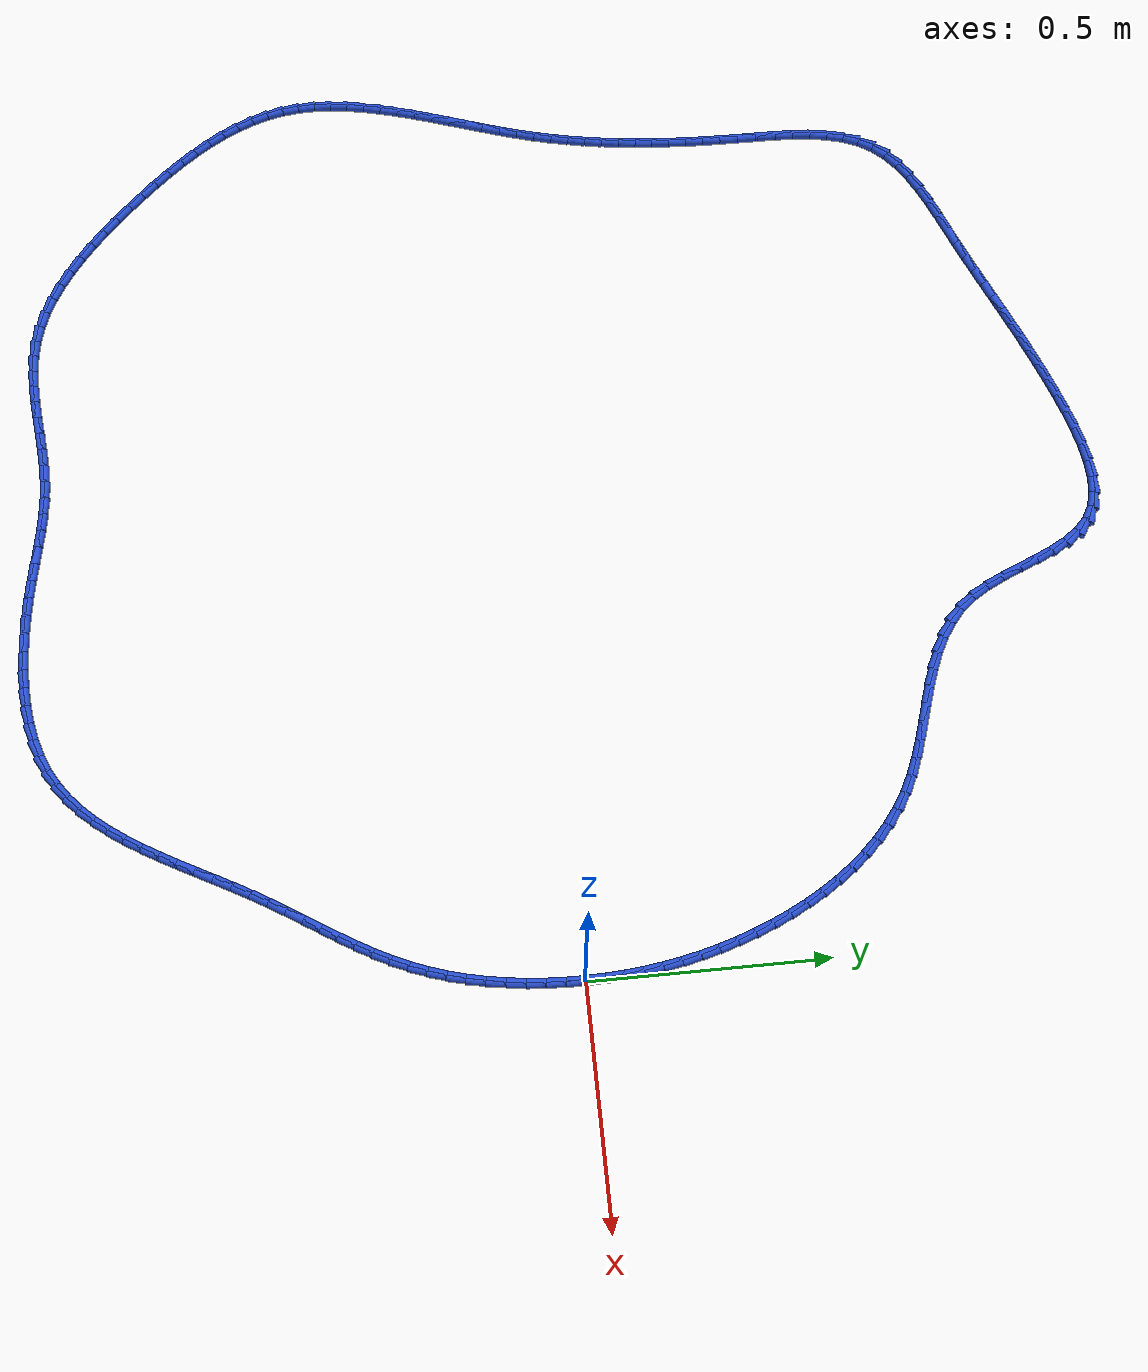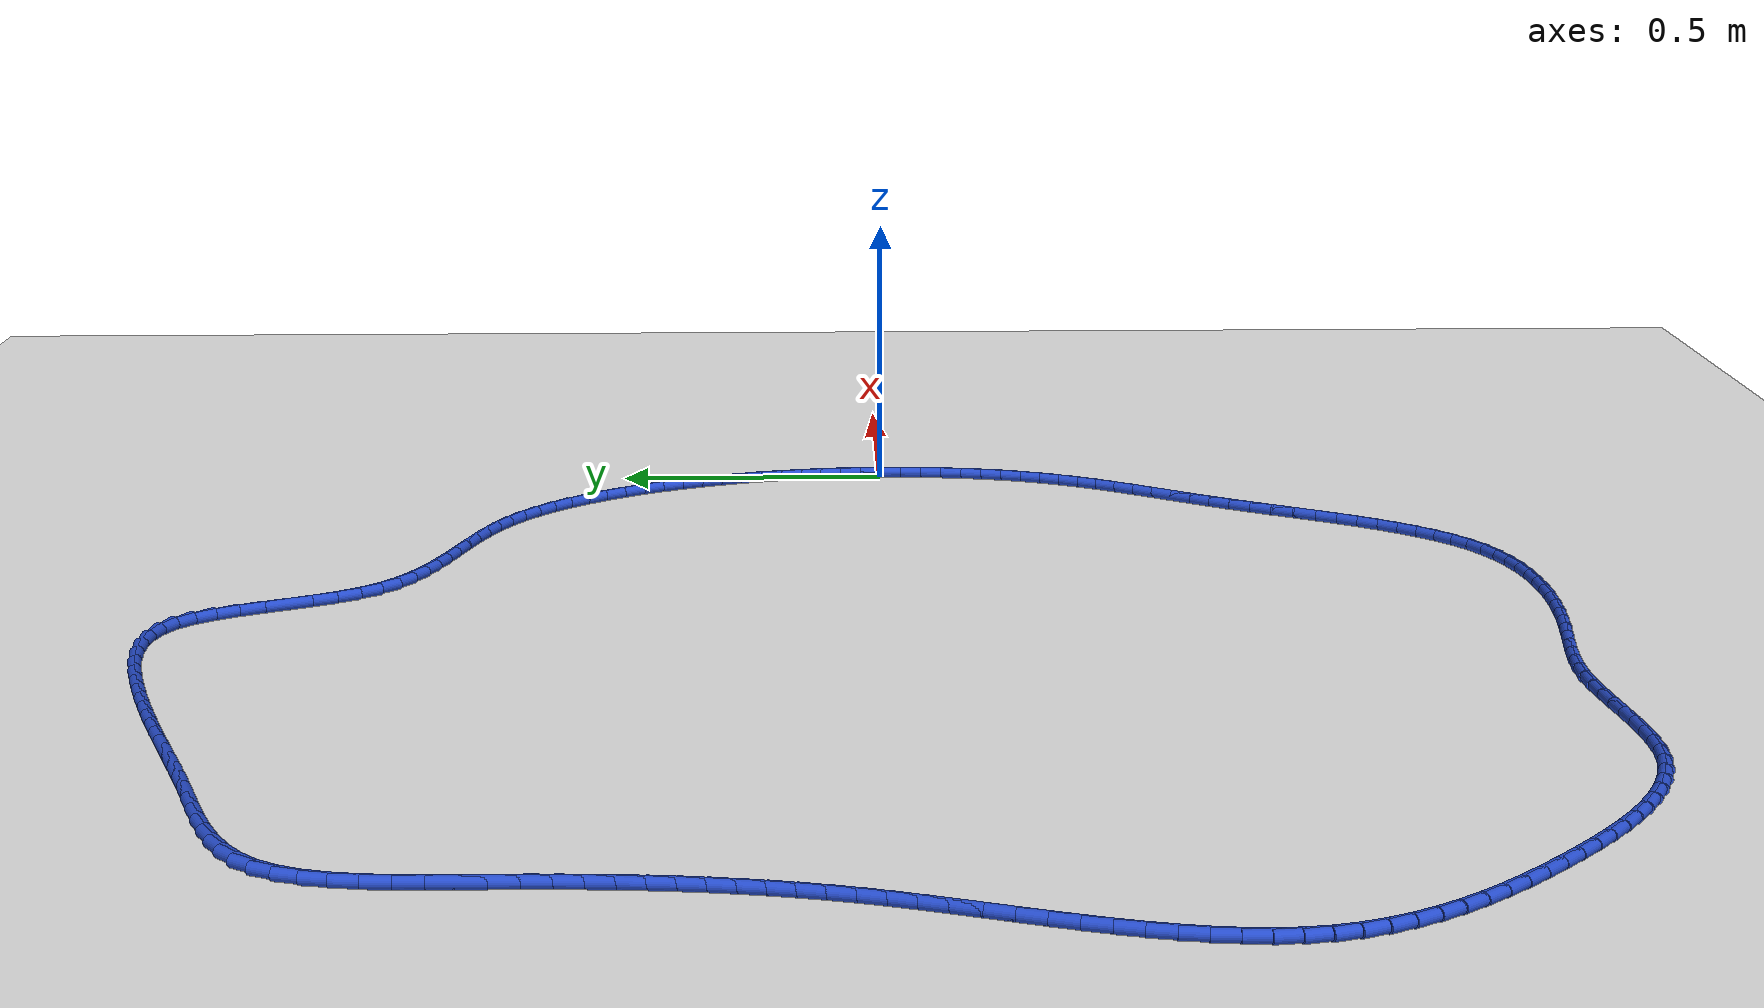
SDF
<sdf version="1.6">
 <world name="default">
  <light name="sun" type="directional">
   <pose>0 0 10 0 -0 0</pose>
   <diffuse>0.8 0.8 0.8 1</diffuse>
   <specular>0.2 0.2 0.2 1</specular>
   <attenuation>
    <range>1000</range>
    <constant>0.9</constant>
    <linear>0.01</linear>
    <quadratic>0.001</quadratic>
   </attenuation>
   <direction>-0.5 0.1 -0.9</direction>
  </light>
  <model name="ground_plane">
   <static>1</static>
   <link name="link">
    <collision name="collision">
     <geometry><plane><normal>0 0 1</normal><size>100 100</size></plane></geometry>
     <surface><friction><ode><mu>100</mu><mu2>50</mu2></ode></friction></surface>
    </collision>
    <visual name="visual">
     <cast_shadows>0</cast_shadows>
     <geometry><plane><normal>0 0 1</normal><size>100 100</size></plane></geometry>
     <material>
      <script><uri>file://media/materials/scripts/gazebo.material</uri><name>Gazebo/WhiteGlow</name></script>
     </material>
    </visual>
   </link>
  </model>
  <gravity>0 0 -9.8</gravity>
  <magnetic_field>6e-06 2.3e-05 -4.2e-05</magnetic_field>
  <atmosphere type="adiabatic"/>
  <physics name="default_physics" default="0" type="ode">
   <max_step_size>0.001</max_step_size>
   <real_time_factor>1</real_time_factor>
   <real_time_update_rate>1000</real_time_update_rate>
  </physics>
  <scene><ambient>0.4 0.4 0.4 1</ambient><background>0.7 0.7 0.7 1</background><shadows>1</shadows></scene>
  <spherical_coordinates>
   <surface_model>EARTH_WGS84</surface_model>
   <latitude_deg>0</latitude_deg>
   <longitude_deg>0</longitude_deg>
   <elevation>0</elevation>
   <heading_deg>0</heading_deg>
  </spherical_coordinates>
  <model name="line">
   <link name="link_0">
    <pose>-6.071532165918825e-18 6.938893903907228e-18 0.01 0 1.57 -1.5463985044443407</pose>
    <collision name="collision">
     <geometry><cylinder><radius>0.01</radius><length>0.08</length></cylinder></geometry>
    </collision>
    <visual name="visual">
     <material>
      <script><name>Gazebo/Blue</name><uri>file://media/materials/scripts/gazebo.material</uri></script>
     </material>
     <geometry><cylinder><radius>0.01</radius><length>0.08</length></cylinder></geometry>
    </visual>
   </link>
   <link name="link_1">
    <pose>-0.0009689574108318324 0.03970703330716391 0.01 0 1.57 -1.5098031776221879</pose>
    <collision name="collision">
     <geometry><cylinder><radius>0.01</radius><length>0.08</length></cylinder></geometry>
    </collision>
    <visual name="visual">
     <material>
      <script><name>Gazebo/Blue</name><uri>file://media/materials/scripts/gazebo.material</uri></script>
     </material>
     <geometry><cylinder><radius>0.01</radius><length>0.08</length></cylinder></geometry>
    </visual>
   </link>
   <link name="link_2">
    <pose>-0.0033803758794193413 0.07919388500188519 0.01 0 1.57 -1.472248625345816</pose>
    <collision name="collision">
     <geometry><cylinder><radius>0.01</radius><length>0.08</length></cylinder></geometry>
    </collision>
    <visual name="visual">
     <material>
      <script><name>Gazebo/Blue</name><uri>file://media/materials/scripts/gazebo.material</uri></script>
     </material>
     <geometry><cylinder><radius>0.01</radius><length>0.08</length></cylinder></geometry>
    </visual>
   </link>
   <link name="link_3">
    <pose>-0.007262522352865022 0.11845985390627183 0.01 0 1.57 -1.4338380023221324</pose>
    <collision name="collision">
     <geometry><cylinder><radius>0.01</radius><length>0.08</length></cylinder></geometry>
    </collision>
    <visual name="visual">
     <material>
      <script><name>Gazebo/Blue</name><uri>file://media/materials/scripts/gazebo.material</uri></script>
     </material>
     <geometry><cylinder><radius>0.01</radius><length>0.08</length></cylinder></geometry>
    </visual>
   </link>
   <link name="link_4">
    <pose>-0.012643663778271357 0.1575042388424318 0.01 0 1.57 -1.3946894940632477</pose>
    <collision name="collision">
     <geometry><cylinder><radius>0.01</radius><length>0.08</length></cylinder></geometry>
    </collision>
    <visual name="visual">
     <material>
      <script><name>Gazebo/Blue</name><uri>file://media/materials/scripts/gazebo.material</uri></script>
     </material>
     <geometry><cylinder><radius>0.01</radius><length>0.08</length></cylinder></geometry>
    </visual>
   </link>
   <link name="link_5">
    <pose>-0.01955206710274083 0.196326338632473 0.01 0 1.57 -1.3549348991201096</pose>
    <collision name="collision">
     <geometry><cylinder><radius>0.01</radius><length>0.08</length></cylinder></geometry>
    </collision>
    <visual name="visual">
     <material>
      <script><name>Gazebo/Blue</name><uri>file://media/materials/scripts/gazebo.material</uri></script>
     </material>
     <geometry><cylinder><radius>0.01</radius><length>0.08</length></cylinder></geometry>
    </visual>
   </link>
   <link name="link_6">
    <pose>-0.028015999273375912 0.23492545209850355 0.01 0 1.57 -1.3147175864154095</pose>
    <collision name="collision">
     <geometry><cylinder><radius>0.01</radius><length>0.08</length></cylinder></geometry>
    </collision>
    <visual name="visual">
     <material>
      <script><name>Gazebo/Blue</name><uri>file://media/materials/scripts/gazebo.material</uri></script>
     </material>
     <geometry><cylinder><radius>0.01</radius><length>0.08</length></cylinder></geometry>
    </visual>
   </link>
   <link name="link_7">
    <pose>-0.03806372723727911 0.27330087806263126 0.01 0 1.57 -1.2741898827602673</pose>
    <collision name="collision">
     <geometry><cylinder><radius>0.01</radius><length>0.08</length></cylinder></geometry>
    </collision>
    <visual name="visual">
     <material>
      <script><name>Gazebo/Blue</name><uri>file://media/materials/scripts/gazebo.material</uri></script>
     </material>
     <geometry><cylinder><radius>0.01</radius><length>0.08</length></cylinder></geometry>
    </visual>
   </link>
   <link name="link_8">
    <pose>-0.049723517941552886 0.3114519153469641 0.01 0 1.57 -1.233507411304486</pose>
    <collision name="collision">
     <geometry><cylinder><radius>0.01</radius><length>0.08</length></cylinder></geometry>
    </collision>
    <visual name="visual">
     <material>
      <script><name>Gazebo/Blue</name><uri>file://media/materials/scripts/gazebo.material</uri></script>
     </material>
     <geometry><cylinder><radius>0.01</radius><length>0.08</length></cylinder></geometry>
    </visual>
   </link>
   <link name="link_9">
    <pose>-0.06302364483047866 0.34937756747782184 0.01 0 1.57 -1.1921834135835399</pose>
    <collision name="collision">
     <geometry><cylinder><radius>0.01</radius><length>0.08</length></cylinder></geometry>
    </collision>
    <visual name="visual">
     <material>
      <script><name>Gazebo/Blue</name><uri>file://media/materials/scripts/gazebo.material</uri></script>
     </material>
     <geometry><cylinder><radius>0.01</radius><length>0.08</length></cylinder></geometry>
    </visual>
   </link>
   <link name="link_10">
    <pose>-0.07799386094021594 0.38700959075672176 0.01 0 1.57 -1.1486053949267057</pose>
    <collision name="collision">
     <geometry><cylinder><radius>0.01</radius><length>0.08</length></cylinder></geometry>
    </collision>
    <visual name="visual">
     <material>
      <script><name>Gazebo/Blue</name><uri>file://media/materials/scripts/gazebo.material</uri></script>
     </material>
     <geometry><cylinder><radius>0.01</radius><length>0.08</length></cylinder></geometry>
    </visual>
   </link>
   <link name="link_11">
    <pose>-0.09466727212605346 0.4241273563680289 0.01 0 1.57 -1.1021181854967506</pose>
    <collision name="collision">
     <geometry><cylinder><radius>0.01</radius><length>0.08</length></cylinder></geometry>
    </collision>
    <visual name="visual">
     <material>
      <script><name>Gazebo/Blue</name><uri>file://media/materials/scripts/gazebo.material</uri></script>
     </material>
     <geometry><cylinder><radius>0.01</radius><length>0.08</length></cylinder></geometry>
    </visual>
   </link>
   <link name="link_12">
    <pose>-0.11307744601664074 0.4604892479674049 0.01 0 1.57 -1.0522414140331564</pose>
    <collision name="collision">
     <geometry><cylinder><radius>0.01</radius><length>0.08</length></cylinder></geometry>
    </collision>
    <visual name="visual">
     <material>
      <script><name>Gazebo/Blue</name><uri>file://media/materials/scripts/gazebo.material</uri></script>
     </material>
     <geometry><cylinder><radius>0.01</radius><length>0.08</length></cylinder></geometry>
    </visual>
   </link>
   <link name="link_13">
    <pose>-0.1332579502406276 0.49585364921051145 0.01 0 1.57 -0.998490868550117</pose>
    <collision name="collision">
     <geometry><cylinder><radius>0.01</radius><length>0.08</length></cylinder></geometry>
    </collision>
    <visual name="visual">
     <material>
      <script><name>Gazebo/Blue</name><uri>file://media/materials/scripts/gazebo.material</uri></script>
     </material>
     <geometry><cylinder><radius>0.01</radius><length>0.08</length></cylinder></geometry>
    </visual>
   </link>
   <link name="link_14">
    <pose>-0.15524235242666343 0.5299789437530096 0.01 0 1.57 -0.9403918382312176</pose>
    <collision name="collision">
     <geometry><cylinder><radius>0.01</radius><length>0.08</length></cylinder></geometry>
    </collision>
    <visual name="visual">
     <material>
      <script><name>Gazebo/Blue</name><uri>file://media/materials/scripts/gazebo.material</uri></script>
     </material>
     <geometry><cylinder><radius>0.01</radius><length>0.08</length></cylinder></geometry>
    </visual>
   </link>
   <link name="link_15">
    <pose>-0.17906422020339802 0.5626235152505611 0.01 0 1.57 -0.8775031374997446</pose>
    <collision name="collision">
     <geometry><cylinder><radius>0.01</radius><length>0.08</length></cylinder></geometry>
    </collision>
    <visual name="visual">
     <material>
      <script><name>Gazebo/Blue</name><uri>file://media/materials/scripts/gazebo.material</uri></script>
     </material>
     <geometry><cylinder><radius>0.01</radius><length>0.08</length></cylinder></geometry>
    </visual>
   </link>
   <link name="link_16">
    <pose>-0.20475712119948097 0.5935457473588276 0.01 0 1.57 -0.8094542735155562</pose>
    <collision name="collision">
     <geometry><cylinder><radius>0.01</radius><length>0.08</length></cylinder></geometry>
    </collision>
    <visual name="visual">
     <material>
      <script><name>Gazebo/Blue</name><uri>file://media/materials/scripts/gazebo.material</uri></script>
     </material>
     <geometry><cylinder><radius>0.01</radius><length>0.08</length></cylinder></geometry>
    </visual>
   </link>
   <link name="link_17">
    <pose>-0.23235462304356186 0.6225040237334702 0.01 0 1.57 -0.7359971677160898</pose>
    <collision name="collision">
     <geometry><cylinder><radius>0.01</radius><length>0.08</length></cylinder></geometry>
    </collision>
    <visual name="visual">
     <material>
      <script><name>Gazebo/Blue</name><uri>file://media/materials/scripts/gazebo.material</uri></script>
     </material>
     <geometry><cylinder><radius>0.01</radius><length>0.08</length></cylinder></geometry>
    </visual>
   </link>
   <link name="link_18">
    <pose>-0.2618902933642904 0.6492567280301507 0.01 0 1.57 -0.6570710028706424</pose>
    <collision name="collision">
     <geometry><cylinder><radius>0.01</radius><length>0.08</length></cylinder></geometry>
    </collision>
    <visual name="visual">
     <material>
      <script><name>Gazebo/Blue</name><uri>file://media/materials/scripts/gazebo.material</uri></script>
     </material>
     <geometry><cylinder><radius>0.01</radius><length>0.08</length></cylinder></geometry>
    </visual>
   </link>
   <link name="link_19">
    <pose>-0.29339769979031627 0.6735622439045305 0.01 0 1.57 -0.5728735951414075</pose>
    <collision name="collision">
     <geometry><cylinder><radius>0.01</radius><length>0.08</length></cylinder></geometry>
    </collision>
    <visual name="visual">
     <material>
      <script><name>Gazebo/Blue</name><uri>file://media/materials/scripts/gazebo.material</uri></script>
     </material>
     <geometry><cylinder><radius>0.01</radius><length>0.08</length></cylinder></geometry>
    </visual>
   </link>
   <link name="link_20">
    <pose>-0.3269104099502889 0.695178955012271 0.01 0 1.57 -0.48507084203879447</pose>
    <collision name="collision">
     <geometry><cylinder><radius>0.01</radius><length>0.08</length></cylinder></geometry>
    </collision>
    <visual name="visual">
     <material>
      <script><name>Gazebo/Blue</name><uri>file://media/materials/scripts/gazebo.material</uri></script>
     </material>
     <geometry><cylinder><radius>0.01</radius><length>0.08</length></cylinder></geometry>
    </visual>
   </link>
   <link name="link_21">
    <pose>-0.3624384793365288 0.7139048475493727 0.01 0 1.57 -0.4094496652397565</pose>
    <collision name="collision">
     <geometry><cylinder><radius>0.01</radius><length>0.08</length></cylinder></geometry>
    </collision>
    <visual name="visual">
     <material>
      <script><name>Gazebo/Blue</name><uri>file://media/materials/scripts/gazebo.material</uri></script>
     </material>
     <geometry><cylinder><radius>0.01</radius><length>0.08</length></cylinder></geometry>
    </visual>
   </link>
   <link name="link_22">
    <pose>-0.3996783705255612 0.7300661062525278 0.01 0 1.57 -0.3562463981521785</pose>
    <collision name="collision">
     <geometry><cylinder><radius>0.01</radius><length>0.08</length></cylinder></geometry>
    </collision>
    <visual name="visual">
     <material>
      <script><name>Gazebo/Blue</name><uri>file://media/materials/scripts/gazebo.material</uri></script>
     </material>
     <geometry><cylinder><radius>0.01</radius><length>0.08</length></cylinder></geometry>
    </visual>
   </link>
   <link name="link_23">
    <pose>-0.43810330725202734 0.744364927000805 0.01 0 1.57 -0.3245230998444246</pose>
    <collision name="collision">
     <geometry><cylinder><radius>0.01</radius><length>0.08</length></cylinder></geometry>
    </collision>
    <visual name="visual">
     <material>
      <script><name>Gazebo/Blue</name><uri>file://media/materials/scripts/gazebo.material</uri></script>
     </material>
     <geometry><cylinder><radius>0.01</radius><length>0.08</length></cylinder></geometry>
    </visual>
   </link>
   <link name="link_24">
    <pose>-0.477181728764517 0.7575115643966147 0.01 0 1.57 -0.3134148171744887</pose>
    <collision name="collision">
     <geometry><cylinder><radius>0.01</radius><length>0.08</length></cylinder></geometry>
    </collision>
    <visual name="visual">
     <material>
      <script><name>Gazebo/Blue</name><uri>file://media/materials/scripts/gazebo.material</uri></script>
     </material>
     <geometry><cylinder><radius>0.01</radius><length>0.08</length></cylinder></geometry>
    </visual>
   </link>
   <link name="link_25">
    <pose>-0.51638207431162 0.7702162730423666 0.01 0 1.57 -0.322743205539177</pose>
    <collision name="collision">
     <geometry><cylinder><radius>0.01</radius><length>0.08</length></cylinder></geometry>
    </collision>
    <visual name="visual">
     <material>
      <script><name>Gazebo/Blue</name><uri>file://media/materials/scripts/gazebo.material</uri></script>
     </material>
     <geometry><cylinder><radius>0.01</radius><length>0.08</length></cylinder></geometry>
    </visual>
   </link>
   <link name="link_26">
    <pose>-0.5551727831419265 0.7831893075404717 0.01 0 1.57 -0.3531545702912088</pose>
    <collision name="collision">
     <geometry><cylinder><radius>0.01</radius><length>0.08</length></cylinder></geometry>
    </collision>
    <visual name="visual">
     <material>
      <script><name>Gazebo/Blue</name><uri>file://media/materials/scripts/gazebo.material</uri></script>
     </material>
     <geometry><cylinder><radius>0.01</radius><length>0.08</length></cylinder></geometry>
    </visual>
   </link>
   <link name="link_27">
    <pose>-0.5930222945040258 0.7971409224933389 0.01 0 1.57 -0.40606200811253595</pose>
    <collision name="collision">
     <geometry><cylinder><radius>0.01</radius><length>0.08</length></cylinder></geometry>
    </collision>
    <visual name="visual">
     <material>
      <script><name>Gazebo/Blue</name><uri>file://media/materials/scripts/gazebo.material</uri></script>
     </material>
     <geometry><cylinder><radius>0.01</radius><length>0.08</length></cylinder></geometry>
    </visual>
   </link>
   <link name="link_28">
    <pose>-0.6293990476465084 0.8127813725033798 0.01 0 1.57 -0.4833104177553932</pose>
    <collision name="collision">
     <geometry><cylinder><radius>0.01</radius><length>0.08</length></cylinder></geometry>
    </collision>
    <visual name="visual">
     <material>
      <script><name>Gazebo/Blue</name><uri>file://media/materials/scripts/gazebo.material</uri></script>
     </material>
     <geometry><cylinder><radius>0.01</radius><length>0.08</length></cylinder></geometry>
    </visual>
   </link>
   <link name="link_29">
    <pose>-0.6637714818179637 0.8308209121730035 0.01 0 1.57 -0.5863593184405562</pose>
    <collision name="collision">
     <geometry><cylinder><radius>0.01</radius><length>0.08</length></cylinder></geometry>
    </collision>
    <visual name="visual">
     <material>
      <script><name>Gazebo/Blue</name><uri>file://media/materials/scripts/gazebo.material</uri></script>
     </material>
     <geometry><cylinder><radius>0.01</radius><length>0.08</length></cylinder></geometry>
    </visual>
   </link>
   <link name="link_30">
    <pose>-0.6956080362669816 0.8519697961046208 0.01 0 1.57 -0.7147899993734204</pose>
    <collision name="collision">
     <geometry><cylinder><radius>0.01</radius><length>0.08</length></cylinder></geometry>
    </collision>
    <visual name="visual">
     <material>
      <script><name>Gazebo/Blue</name><uri>file://media/materials/scripts/gazebo.material</uri></script>
     </material>
     <geometry><cylinder><radius>0.01</radius><length>0.08</length></cylinder></geometry>
    </visual>
   </link>
   <link name="link_31">
    <pose>-0.7243771502421518 0.8769382789006412 0.01 0 1.57 -0.8642650642933042</pose>
    <collision name="collision">
     <geometry><cylinder><radius>0.01</radius><length>0.08</length></cylinder></geometry>
    </collision>
    <visual name="visual">
     <material>
      <script><name>Gazebo/Blue</name><uri>file://media/materials/scripts/gazebo.material</uri></script>
     </material>
     <geometry><cylinder><radius>0.01</radius><length>0.08</length></cylinder></geometry>
    </visual>
   </link>
   <link name="link_32">
    <pose>-0.74955052460423 0.9064320423052483 0.01 0 1.57 -1.0069290822484311</pose>
    <collision name="collision">
     <geometry><cylinder><radius>0.01</radius><length>0.08</length></cylinder></geometry>
    </collision>
    <visual name="visual">
     <material>
      <script><name>Gazebo/Blue</name><uri>file://media/materials/scripts/gazebo.material</uri></script>
     </material>
     <geometry><cylinder><radius>0.01</radius><length>0.08</length></cylinder></geometry>
    </visual>
   </link>
   <link name="link_33">
    <pose>-0.7710816044281747 0.9404813511578508 0.01 0 1.57 -1.1028026650929452</pose>
    <collision name="collision">
     <geometry><cylinder><radius>0.01</radius><length>0.08</length></cylinder></geometry>
    </collision>
    <visual name="visual">
     <material>
      <script><name>Gazebo/Blue</name><uri>file://media/materials/scripts/gazebo.material</uri></script>
     </material>
     <geometry><cylinder><radius>0.01</radius><length>0.08</length></cylinder></geometry>
    </visual>
   </link>
   <link name="link_34">
    <pose>-0.7899103915508144 0.9777332941333323 0.01 0 1.57 -1.1550617997431303</pose>
    <collision name="collision">
     <geometry><cylinder><radius>0.01</radius><length>0.08</length></cylinder></geometry>
    </collision>
    <visual name="visual">
     <material>
      <script><name>Gazebo/Blue</name><uri>file://media/materials/scripts/gazebo.material</uri></script>
     </material>
     <geometry><cylinder><radius>0.01</radius><length>0.08</length></cylinder></geometry>
    </visual>
   </link>
   <link name="link_35">
    <pose>-0.8070976851413235 1.0166655991588731 0.01 0 1.57 -1.169073434816772</pose>
    <collision name="collision">
     <geometry><cylinder><radius>0.01</radius><length>0.08</length></cylinder></geometry>
    </collision>
    <visual name="visual">
     <material>
      <script><name>Gazebo/Blue</name><uri>file://media/materials/scripts/gazebo.material</uri></script>
     </material>
     <geometry><cylinder><radius>0.01</radius><length>0.08</length></cylinder></geometry>
    </visual>
   </link>
   <link name="link_36">
    <pose>-0.8237042843688773 1.0557559941616546 0.01 0 1.57 -1.1455223311910874</pose>
    <collision name="collision">
     <geometry><cylinder><radius>0.01</radius><length>0.08</length></cylinder></geometry>
    </collision>
    <visual name="visual">
     <material>
      <script><name>Gazebo/Blue</name><uri>file://media/materials/scripts/gazebo.material</uri></script>
     </material>
     <geometry><cylinder><radius>0.01</radius><length>0.08</length></cylinder></geometry>
    </visual>
   </link>
   <link name="link_37">
    <pose>-0.8407909884026502 1.0934822070688575 0.01 0 1.57 -1.0798026215874026</pose>
    <collision name="collision">
     <geometry><cylinder><radius>0.01</radius><length>0.08</length></cylinder></geometry>
    </collision>
    <visual name="visual">
     <material>
      <script><name>Gazebo/Blue</name><uri>file://media/materials/scripts/gazebo.material</uri></script>
     </material>
     <geometry><cylinder><radius>0.01</radius><length>0.08</length></cylinder></geometry>
    </visual>
   </link>
   <link name="link_38">
    <pose>-0.8594185964118172 1.1283219658076618 0.01 0 1.57 -0.9616691492078544</pose>
    <collision name="collision">
     <geometry><cylinder><radius>0.01</radius><length>0.08</length></cylinder></geometry>
    </collision>
    <visual name="visual">
     <material>
      <script><name>Gazebo/Blue</name><uri>file://media/materials/scripts/gazebo.material</uri></script>
     </material>
     <geometry><cylinder><radius>0.01</radius><length>0.08</length></cylinder></geometry>
    </visual>
   </link>
   <link name="link_39">
    <pose>-0.8806479075655538 1.15875299830525 0.01 0 1.57 -0.7774662660042144</pose>
    <collision name="collision">
     <geometry><cylinder><radius>0.01</radius><length>0.08</length></cylinder></geometry>
    </collision>
    <visual name="visual">
     <material>
      <script><name>Gazebo/Blue</name><uri>file://media/materials/scripts/gazebo.material</uri></script>
     </material>
     <geometry><cylinder><radius>0.01</radius><length>0.08</length></cylinder></geometry>
    </visual>
   </link>
   <link name="link_40">
    <pose>-0.905539721033034 1.1832530324888015 0.01 0 1.57 -0.5284871922387998</pose>
    <collision name="collision">
     <geometry><cylinder><radius>0.01</radius><length>0.08</length></cylinder></geometry>
    </collision>
    <visual name="visual">
     <material>
      <script><name>Gazebo/Blue</name><uri>file://media/materials/scripts/gazebo.material</uri></script>
     </material>
     <geometry><cylinder><radius>0.01</radius><length>0.08</length></cylinder></geometry>
    </visual>
   </link>
   <link name="link_41">
    <pose>-0.9350244809831206 1.2004687904364246 0.01 0 1.57 -0.28943613146975444</pose>
    <collision name="collision">
     <geometry><cylinder><radius>0.01</radius><length>0.08</length></cylinder></geometry>
    </collision>
    <visual name="visual">
     <material>
      <script><name>Gazebo/Blue</name><uri>file://media/materials/scripts/gazebo.material</uri></script>
     </material>
     <geometry><cylinder><radius>0.01</radius><length>0.08</length></cylinder></geometry>
    </visual>
   </link>
   <link name="link_42">
    <pose>-0.96887395262844 1.2105491227670186 0.01 0 1.57 -0.10344830354783854</pose>
    <collision name="collision">
     <geometry><cylinder><radius>0.01</radius><length>0.08</length></cylinder></geometry>
    </collision>
    <visual name="visual">
     <material>
      <script><name>Gazebo/Blue</name><uri>file://media/materials/scripts/gazebo.material</uri></script>
     </material>
     <geometry><cylinder><radius>0.01</radius><length>0.08</length></cylinder></geometry>
    </visual>
   </link>
   <link name="link_43">
    <pose>-1.0062529293540954 1.2144297673564552 0.01 0 1.57 0.03433789562780403</pose>
    <collision name="collision">
     <geometry><cylinder><radius>0.01</radius><length>0.08</length></cylinder></geometry>
    </collision>
    <visual name="visual">
     <material>
      <script><name>Gazebo/Blue</name><uri>file://media/materials/scripts/gazebo.material</uri></script>
     </material>
     <geometry><cylinder><radius>0.01</radius><length>0.08</length></cylinder></geometry>
    </visual>
   </link>
   <link name="link_44">
    <pose>-1.0463208702193758 1.2130533775795067 0.01 0 1.57 0.1349398559998989</pose>
    <collision name="collision">
     <geometry><cylinder><radius>0.01</radius><length>0.08</length></cylinder></geometry>
    </collision>
    <visual name="visual">
     <material>
      <script><name>Gazebo/Blue</name><uri>file://media/materials/scripts/gazebo.material</uri></script>
     </material>
     <geometry><cylinder><radius>0.01</radius><length>0.08</length></cylinder></geometry>
    </visual>
   </link>
   <link name="link_45">
    <pose>-1.0882372342835709 1.2073626068109464 0.01 0 1.57 0.2080720398100845</pose>
    <collision name="collision">
     <geometry><cylinder><radius>0.01</radius><length>0.08</length></cylinder></geometry>
    </collision>
    <visual name="visual">
     <material>
      <script><name>Gazebo/Blue</name><uri>file://media/materials/scripts/gazebo.material</uri></script>
     </material>
     <geometry><cylinder><radius>0.01</radius><length>0.08</length></cylinder></geometry>
    </visual>
   </link>
   <link name="link_46">
    <pose>-1.131161480605971 1.1983001084255478 0.01 0 1.57 0.26061284737794516</pose>
    <collision name="collision">
     <geometry><cylinder><radius>0.01</radius><length>0.08</length></cylinder></geometry>
    </collision>
    <visual name="visual">
     <material>
      <script><name>Gazebo/Blue</name><uri>file://media/materials/scripts/gazebo.material</uri></script>
     </material>
     <geometry><cylinder><radius>0.01</radius><length>0.08</length></cylinder></geometry>
    </visual>
   </link>
   <link name="link_47">
    <pose>-1.174253068245865 1.1868085357980833 0.01 0 1.57 0.2969084215899622</pose>
    <collision name="collision">
     <geometry><cylinder><radius>0.01</radius><length>0.08</length></cylinder></geometry>
    </collision>
    <visual name="visual">
     <material>
      <script><name>Gazebo/Blue</name><uri>file://media/materials/scripts/gazebo.material</uri></script>
     </material>
     <geometry><cylinder><radius>0.01</radius><length>0.08</length></cylinder></geometry>
    </visual>
   </link>
   <link name="link_48">
    <pose>-1.2166714562625425 1.1738305423033266 0.01 0 1.57 0.3197451185368244</pose>
    <collision name="collision">
     <geometry><cylinder><radius>0.01</radius><length>0.08</length></cylinder></geometry>
    </collision>
    <visual name="visual">
     <material>
      <script><name>Gazebo/Blue</name><uri>file://media/materials/scripts/gazebo.material</uri></script>
     </material>
     <geometry><cylinder><radius>0.01</radius><length>0.08</length></cylinder></geometry>
    </visual>
   </link>
   <link name="link_49">
    <pose>-1.2576208942513718 1.1602719148865517 0.01 0 1.57 0.3363572651538081</pose>
    <collision name="collision">
     <geometry><cylinder><radius>0.01</radius><length>0.08</length></cylinder></geometry>
    </collision>
    <visual name="visual">
     <material>
      <script><name>Gazebo/Blue</name><uri>file://media/materials/scripts/gazebo.material</uri></script>
     </material>
     <geometry><cylinder><radius>0.01</radius><length>0.08</length></cylinder></geometry>
    </visual>
   </link>
   <link name="link_50">
    <pose>-1.2969232283403034 1.1465301058978143 0.01 0 1.57 0.35124207204506946</pose>
    <collision name="collision">
     <geometry><cylinder><radius>0.01</radius><length>0.08</length></cylinder></geometry>
    </collision>
    <visual name="visual">
     <material>
      <script><name>Gazebo/Blue</name><uri>file://media/materials/scripts/gazebo.material</uri></script>
     </material>
     <geometry><cylinder><radius>0.01</radius><length>0.08</length></cylinder></geometry>
    </visual>
   </link>
   <link name="link_51">
    <pose>-1.3348501872318437 1.1326322759766982 0.01 0 1.57 0.36405639515233956</pose>
    <collision name="collision">
     <geometry><cylinder><radius>0.01</radius><length>0.08</length></cylinder></geometry>
    </collision>
    <visual name="visual">
     <material>
      <script><name>Gazebo/Blue</name><uri>file://media/materials/scripts/gazebo.material</uri></script>
     </material>
     <geometry><cylinder><radius>0.01</radius><length>0.08</length></cylinder></geometry>
    </visual>
   </link>
   <link name="link_52">
    <pose>-1.3716836881841719 1.1185971997129116 0.01 0 1.57 0.3743832435007732</pose>
    <collision name="collision">
     <geometry><cylinder><radius>0.01</radius><length>0.08</length></cylinder></geometry>
    </collision>
    <visual name="visual">
     <material>
      <script><name>Gazebo/Blue</name><uri>file://media/materials/scripts/gazebo.material</uri></script>
     </material>
     <geometry><cylinder><radius>0.01</radius><length>0.08</length></cylinder></geometry>
    </visual>
   </link>
   <link name="link_53">
    <pose>-1.407705648455466 1.104443651696164 0.01 0 1.57 0.38187334571462195</pose>
    <collision name="collision">
     <geometry><cylinder><radius>0.01</radius><length>0.08</length></cylinder></geometry>
    </collision>
    <visual name="visual">
     <material>
      <script><name>Gazebo/Blue</name><uri>file://media/materials/scripts/gazebo.material</uri></script>
     </material>
     <geometry><cylinder><radius>0.01</radius><length>0.08</length></cylinder></geometry>
    </visual>
   </link>
   <link name="link_54">
    <pose>-1.4431979853039065 1.0901904065161647 0.01 0 1.57 0.3862731579008805</pose>
    <collision name="collision">
     <geometry><cylinder><radius>0.01</radius><length>0.08</length></cylinder></geometry>
    </collision>
    <visual name="visual">
     <material>
      <script><name>Gazebo/Blue</name><uri>file://media/materials/scripts/gazebo.material</uri></script>
     </material>
     <geometry><cylinder><radius>0.01</radius><length>0.08</length></cylinder></geometry>
    </visual>
   </link>
   <link name="link_55">
    <pose>-1.478442615987672 1.075856238762622 0.01 0 1.57 0.38744577085603676</pose>
    <collision name="collision">
     <geometry><cylinder><radius>0.01</radius><length>0.08</length></cylinder></geometry>
    </collision>
    <visual name="visual">
     <material>
      <script><name>Gazebo/Blue</name><uri>file://media/materials/scripts/gazebo.material</uri></script>
     </material>
     <geometry><cylinder><radius>0.01</radius><length>0.08</length></cylinder></geometry>
    </visual>
   </link>
   <link name="link_56">
    <pose>-1.513721457764942 1.0614599230252466 0.01 0 1.57 0.38538177856943073</pose>
    <collision name="collision">
     <geometry><cylinder><radius>0.01</radius><length>0.08</length></cylinder></geometry>
    </collision>
    <visual name="visual">
     <material>
      <script><name>Gazebo/Blue</name><uri>file://media/materials/scripts/gazebo.material</uri></script>
     </material>
     <geometry><cylinder><radius>0.01</radius><length>0.08</length></cylinder></geometry>
    </visual>
   </link>
   <link name="link_57">
    <pose>-1.5493164278938945 1.0470202338937458 0.01 0 1.57 0.38019864129182435</pose>
    <collision name="collision">
     <geometry><cylinder><radius>0.01</radius><length>0.08</length></cylinder></geometry>
    </collision>
    <visual name="visual">
     <material>
      <script><name>Gazebo/Blue</name><uri>file://media/materials/scripts/gazebo.material</uri></script>
     </material>
     <geometry><cylinder><radius>0.01</radius><length>0.08</length></cylinder></geometry>
    </visual>
   </link>
   <link name="link_58">
    <pose>-1.585509443632711 1.0325559459578297 0.01 0 1.57 0.3721288148763471</pose>
    <collision name="collision">
     <geometry><cylinder><radius>0.01</radius><length>0.08</length></cylinder></geometry>
    </collision>
    <visual name="visual">
     <material>
      <script><name>Gazebo/Blue</name><uri>file://media/materials/scripts/gazebo.material</uri></script>
     </material>
     <geometry><cylinder><radius>0.01</radius><length>0.08</length></cylinder></geometry>
    </visual>
   </link>
   <link name="link_59">
    <pose>-1.6225824222395688 1.0180858338072074 0.01 0 1.57 0.3618359479437328</pose>
    <collision name="collision">
     <geometry><cylinder><radius>0.01</radius><length>0.08</length></cylinder></geometry>
    </collision>
    <visual name="visual">
     <material>
      <script><name>Gazebo/Blue</name><uri>file://media/materials/scripts/gazebo.material</uri></script>
     </material>
     <geometry><cylinder><radius>0.01</radius><length>0.08</length></cylinder></geometry>
    </visual>
   </link>
   <link name="link_60">
    <pose>-1.6607994734513074 1.0036206659014333 0.01 0 1.57 0.359592009753183</pose>
    <collision name="collision">
     <geometry><cylinder><radius>0.01</radius><length>0.08</length></cylinder></geometry>
    </collision>
    <visual name="visual">
     <material>
      <script><name>Gazebo/Blue</name><uri>file://media/materials/scripts/gazebo.material</uri></script>
     </material>
     <geometry><cylinder><radius>0.01</radius><length>0.08</length></cylinder></geometry>
    </visual>
   </link>
   <link name="link_61">
    <pose>-1.6998830652946877 0.9889276925851633 0.01 0 1.57 0.37646532392815757</pose>
    <collision name="collision">
     <geometry><cylinder><radius>0.01</radius><length>0.08</length></cylinder></geometry>
    </collision>
    <visual name="visual">
     <material>
      <script><name>Gazebo/Blue</name><uri>file://media/materials/scripts/gazebo.material</uri></script>
     </material>
     <geometry><cylinder><radius>0.01</radius><length>0.08</length></cylinder></geometry>
    </visual>
   </link>
   <link name="link_62">
    <pose>-1.7389285703696726 0.9734922267278643 0.01 0 1.57 0.41359460355745054</pose>
    <collision name="collision">
     <geometry><cylinder><radius>0.01</radius><length>0.08</length></cylinder></geometry>
    </collision>
    <visual name="visual">
     <material>
      <script><name>Gazebo/Blue</name><uri>file://media/materials/scripts/gazebo.material</uri></script>
     </material>
     <geometry><cylinder><radius>0.01</radius><length>0.08</length></cylinder></geometry>
    </visual>
   </link>
   <link name="link_63">
    <pose>-1.7769963479530984 0.9567838394673649 0.01 0 1.57 0.4732612441849225</pose>
    <collision name="collision">
     <geometry><cylinder><radius>0.01</radius><length>0.08</length></cylinder></geometry>
    </collision>
    <visual name="visual">
     <material>
      <script><name>Gazebo/Blue</name><uri>file://media/materials/scripts/gazebo.material</uri></script>
     </material>
     <geometry><cylinder><radius>0.01</radius><length>0.08</length></cylinder></geometry>
    </visual>
   </link>
   <link name="link_64">
    <pose>-1.8131467573218012 0.9382721019414945 0.01 0 1.57 0.5594011265303918</pose>
    <collision name="collision">
     <geometry><cylinder><radius>0.01</radius><length>0.08</length></cylinder></geometry>
    </collision>
    <visual name="visual">
     <material>
      <script><name>Gazebo/Blue</name><uri>file://media/materials/scripts/gazebo.material</uri></script>
     </material>
     <geometry><cylinder><radius>0.01</radius><length>0.08</length></cylinder></geometry>
    </visual>
   </link>
   <link name="link_65">
    <pose>-1.8464401577526177 0.9174265852880817 0.01 0 1.57 0.6770585923704274</pose>
    <collision name="collision">
     <geometry><cylinder><radius>0.01</radius><length>0.08</length></cylinder></geometry>
    </collision>
    <visual name="visual">
     <material>
      <script><name>Gazebo/Blue</name><uri>file://media/materials/scripts/gazebo.material</uri></script>
     </material>
     <geometry><cylinder><radius>0.01</radius><length>0.08</length></cylinder></geometry>
    </visual>
   </link>
   <link name="link_66">
    <pose>-1.8759369085223856 0.893716860644956 0.01 0 1.57 0.8305599373830256</pose>
    <collision name="collision">
     <geometry><cylinder><radius>0.01</radius><length>0.08</length></cylinder></geometry>
    </collision>
    <visual name="visual">
     <material>
      <script><name>Gazebo/Blue</name><uri>file://media/materials/scripts/gazebo.material</uri></script>
     </material>
     <geometry><cylinder><radius>0.01</radius><length>0.08</length></cylinder></geometry>
    </visual>
   </link>
   <link name="link_67">
    <pose>-1.9006973689079416 0.8666124991499468 0.01 0 1.57 1.0129136267222016</pose>
    <collision name="collision">
     <geometry><cylinder><radius>0.01</radius><length>0.08</length></cylinder></geometry>
    </collision>
    <visual name="visual">
     <material>
      <script><name>Gazebo/Blue</name><uri>file://media/materials/scripts/gazebo.material</uri></script>
     </material>
     <geometry><cylinder><radius>0.01</radius><length>0.08</length></cylinder></geometry>
    </visual>
   </link>
   <link name="link_68">
    <pose>-1.9199788175189478 0.8357129350241627 0.01 0 1.57 1.1790960409352982</pose>
    <collision name="collision">
     <geometry><cylinder><radius>0.01</radius><length>0.08</length></cylinder></geometry>
    </collision>
    <visual name="visual">
     <material>
      <script><name>Gazebo/Blue</name><uri>file://media/materials/scripts/gazebo.material</uri></script>
     </material>
     <geometry><cylinder><radius>0.01</radius><length>0.08</length></cylinder></geometry>
    </visual>
   </link>
   <link name="link_69">
    <pose>-1.934167271256702 0.8013619754898986 0.01 0 1.57 1.311083215576916</pose>
    <collision name="collision">
     <geometry><cylinder><radius>0.01</radius><length>0.08</length></cylinder></geometry>
    </collision>
    <visual name="visual">
     <material>
      <script><name>Gazebo/Blue</name><uri>file://media/materials/scripts/gazebo.material</uri></script>
     </material>
     <geometry><cylinder><radius>0.01</radius><length>0.08</length></cylinder></geometry>
    </visual>
   </link>
   <link name="link_70">
    <pose>-1.9440501987840721 0.7641681745710868 0.01 0 1.57 1.4107339719890426</pose>
    <collision name="collision">
     <geometry><cylinder><radius>0.01</radius><length>0.08</length></cylinder></geometry>
    </collision>
    <visual name="visual">
     <material>
      <script><name>Gazebo/Blue</name><uri>file://media/materials/scripts/gazebo.material</uri></script>
     </material>
     <geometry><cylinder><radius>0.01</radius><length>0.08</length></cylinder></geometry>
    </visual>
   </link>
   <link name="link_71">
    <pose>-1.950415553395354 0.7247404058932442 0.01 0 1.57 1.4824645061787423</pose>
    <collision name="collision">
     <geometry><cylinder><radius>0.01</radius><length>0.08</length></cylinder></geometry>
    </collision>
    <visual name="visual">
     <material>
      <script><name>Gazebo/Blue</name><uri>file://media/materials/scripts/gazebo.material</uri></script>
     </material>
     <geometry><cylinder><radius>0.01</radius><length>0.08</length></cylinder></geometry>
    </visual>
   </link>
   <link name="link_72">
    <pose>-1.95405128838484 0.6836875430818881 0.01 0 1.57 1.5305493393597656</pose>
    <collision name="collision">
     <geometry><cylinder><radius>0.01</radius><length>0.08</length></cylinder></geometry>
    </collision>
    <visual name="visual">
     <material>
      <script><name>Gazebo/Blue</name><uri>file://media/materials/scripts/gazebo.material</uri></script>
     </material>
     <geometry><cylinder><radius>0.01</radius><length>0.08</length></cylinder></geometry>
    </visual>
   </link>
   <link name="link_73">
    <pose>-1.9557453570468248 0.6416184597625352 0.01 0 1.57 1.5580757078500562</pose>
    <collision name="collision">
     <geometry><cylinder><radius>0.01</radius><length>0.08</length></cylinder></geometry>
    </collision>
    <visual name="visual">
     <material>
      <script><name>Gazebo/Blue</name><uri>file://media/materials/scripts/gazebo.material</uri></script>
     </material>
     <geometry><cylinder><radius>0.01</radius><length>0.08</length></cylinder></geometry>
    </visual>
   </link>
   <link name="link_74">
    <pose>-1.9562857126756021 0.5991420295607026 0.01 0 1.57 1.5666663399741731</pose>
    <collision name="collision">
     <geometry><cylinder><radius>0.01</radius><length>0.08</length></cylinder></geometry>
    </collision>
    <visual name="visual">
     <material>
      <script><name>Gazebo/Blue</name><uri>file://media/materials/scripts/gazebo.material</uri></script>
     </material>
     <geometry><cylinder><radius>0.01</radius><length>0.08</length></cylinder></geometry>
    </visual>
   </link>
   <link name="link_75">
    <pose>-1.9564603084628245 0.5568671260031804 0.01 0 1.57 1.5594205305227684</pose>
    <collision name="collision">
     <geometry><cylinder><radius>0.01</radius><length>0.08</length></cylinder></geometry>
    </collision>
    <visual name="visual">
     <material>
      <script><name>Gazebo/Blue</name><uri>file://media/materials/scripts/gazebo.material</uri></script>
     </material>
     <geometry><cylinder><radius>0.01</radius><length>0.08</length></cylinder></geometry>
    </visual>
   </link>
   <link name="link_76">
    <pose>-1.9569333744017103 0.5152836164971558 0.01 0 1.57 1.547436867257803</pose>
    <collision name="collision">
     <geometry><cylinder><radius>0.01</radius><length>0.08</length></cylinder></geometry>
    </collision>
    <visual name="visual">
     <material>
      <script><name>Gazebo/Blue</name><uri>file://media/materials/scripts/gazebo.material</uri></script>
     </material>
     <geometry><cylinder><radius>0.01</radius><length>0.08</length></cylinder></geometry>
    </visual>
   </link>
   <link name="link_77">
    <pose>-1.9578881304892581 0.47441869747247734 0.01 0 1.57 1.5334602290007382</pose>
    <collision name="collision">
     <geometry><cylinder><radius>0.01</radius><length>0.08</length></cylinder></geometry>
    </collision>
    <visual name="visual">
     <material>
      <script><name>Gazebo/Blue</name><uri>file://media/materials/scripts/gazebo.material</uri></script>
     </material>
     <geometry><cylinder><radius>0.01</radius><length>0.08</length></cylinder></geometry>
    </visual>
   </link>
   <link name="link_78">
    <pose>-1.9593909180990623 0.43418714285770454 0.01 0 1.57 1.517495593245619</pose>
    <collision name="collision">
     <geometry><cylinder><radius>0.01</radius><length>0.08</length></cylinder></geometry>
    </collision>
    <visual name="visual">
     <material>
      <script><name>Gazebo/Blue</name><uri>file://media/materials/scripts/gazebo.material</uri></script>
     </material>
     <geometry><cylinder><radius>0.01</radius><length>0.08</length></cylinder></geometry>
    </visual>
   </link>
   <link name="link_79">
    <pose>-1.9615080786047177 0.39450372658139565 0.01 0 1.57 1.4995799265684002</pose>
    <collision name="collision">
     <geometry><cylinder><radius>0.01</radius><length>0.08</length></cylinder></geometry>
    </collision>
    <visual name="visual">
     <material>
      <script><name>Gazebo/Blue</name><uri>file://media/materials/scripts/gazebo.material</uri></script>
     </material>
     <geometry><cylinder><radius>0.01</radius><length>0.08</length></cylinder></geometry>
    </visual>
   </link>
   <link name="link_80">
    <pose>-1.9643059533798184 0.35528322257210854 0.01 0 1.57 1.479784974454773</pose>
    <collision name="collision">
     <geometry><cylinder><radius>0.01</radius><length>0.08</length></cylinder></geometry>
    </collision>
    <visual name="visual">
     <material>
      <script><name>Gazebo/Blue</name><uri>file://media/materials/scripts/gazebo.material</uri></script>
     </material>
     <geometry><cylinder><radius>0.01</radius><length>0.08</length></cylinder></geometry>
    </visual>
   </link>
   <link name="link_81">
    <pose>-1.9678508837979591 0.3164404047584028 0.01 0 1.57 1.4582189057279142</pose>
    <collision name="collision">
     <geometry><cylinder><radius>0.01</radius><length>0.08</length></cylinder></geometry>
    </collision>
    <visual name="visual">
     <material>
      <script><name>Gazebo/Blue</name><uri>file://media/materials/scripts/gazebo.material</uri></script>
     </material>
     <geometry><cylinder><radius>0.01</radius><length>0.08</length></cylinder></geometry>
    </visual>
   </link>
   <link name="link_82">
    <pose>-1.972209211232734 0.2778900470688364 0.01 0 1.57 1.435026454988793</pose>
    <collision name="collision">
     <geometry><cylinder><radius>0.01</radius><length>0.08</length></cylinder></geometry>
    </collision>
    <visual name="visual">
     <material>
      <script><name>Gazebo/Blue</name><uri>file://media/materials/scripts/gazebo.material</uri></script>
     </material>
     <geometry><cylinder><radius>0.01</radius><length>0.08</length></cylinder></geometry>
    </visual>
   </link>
   <link name="link_83">
    <pose>-1.9774472770577385 0.2395469234319676 0.01 0 1.57 1.4103872773585167</pose>
    <collision name="collision">
     <geometry><cylinder><radius>0.01</radius><length>0.08</length></cylinder></geometry>
    </collision>
    <visual name="visual">
     <material>
      <script><name>Gazebo/Blue</name><uri>file://media/materials/scripts/gazebo.material</uri></script>
     </material>
     <geometry><cylinder><radius>0.01</radius><length>0.08</length></cylinder></geometry>
    </visual>
   </link>
   <link name="link_84">
    <pose>-1.9836314226465668 0.20132580777635578 0.01 0 1.57 1.384512361514638</pose>
    <collision name="collision">
     <geometry><cylinder><radius>0.01</radius><length>0.08</length></cylinder></geometry>
    </collision>
    <visual name="visual">
     <material>
      <script><name>Gazebo/Blue</name><uri>file://media/materials/scripts/gazebo.material</uri></script>
     </material>
     <geometry><cylinder><radius>0.01</radius><length>0.08</length></cylinder></geometry>
    </visual>
   </link>
   <link name="link_85">
    <pose>-1.9908279893728122 0.1631414740305585 0.01 0 1.57 1.3576385315571413</pose>
    <collision name="collision">
     <geometry><cylinder><radius>0.01</radius><length>0.08</length></cylinder></geometry>
    </collision>
    <visual name="visual">
     <material>
      <script><name>Gazebo/Blue</name><uri>file://media/materials/scripts/gazebo.material</uri></script>
     </material>
     <geometry><cylinder><radius>0.01</radius><length>0.08</length></cylinder></geometry>
    </visual>
   </link>
   <link name="link_86">
    <pose>-1.999103318610071 0.12490869612313532 0.01 0 1.57 1.3300212825872042</pose>
    <collision name="collision">
     <geometry><cylinder><radius>0.01</radius><length>0.08</length></cylinder></geometry>
    </collision>
    <visual name="visual">
     <material>
      <script><name>Gazebo/Blue</name><uri>file://media/materials/scripts/gazebo.material</uri></script>
     </material>
     <geometry><cylinder><radius>0.01</radius><length>0.08</length></cylinder></geometry>
    </visual>
   </link>
   <link name="link_87">
    <pose>-2.008523751731936 0.0865422479826442 0.01 0 1.57 1.301931728642851</pose>
    <collision name="collision">
     <geometry><cylinder><radius>0.01</radius><length>0.08</length></cylinder></geometry>
    </collision>
    <visual name="visual">
     <material>
      <script><name>Gazebo/Blue</name><uri>file://media/materials/scripts/gazebo.material</uri></script>
     </material>
     <geometry><cylinder><radius>0.01</radius><length>0.08</length></cylinder></geometry>
    </visual>
   </link>
   <link name="link_88">
    <pose>-2.0191553851367057 0.04795699027958046 0.01 0 1.57 1.2758550231181396</pose>
    <collision name="collision">
     <geometry><cylinder><radius>0.01</radius><length>0.08</length></cylinder></geometry>
    </collision>
    <visual name="visual">
     <material>
      <script><name>Gazebo/Blue</name><uri>file://media/materials/scripts/gazebo.material</uri></script>
     </material>
     <geometry><cylinder><radius>0.01</radius><length>0.08</length></cylinder></geometry>
    </visual>
   </link>
   <link name="link_89">
    <pose>-2.030958640345438 0.009105201512521945 0.01 0 1.57 1.257321574244123</pose>
    <collision name="collision">
     <geometry><cylinder><radius>0.01</radius><length>0.08</length></cylinder></geometry>
    </collision>
    <visual name="visual">
     <material>
      <script><name>Gazebo/Blue</name><uri>file://media/materials/scripts/gazebo.material</uri></script>
     </material>
     <geometry><cylinder><radius>0.01</radius><length>0.08</length></cylinder></geometry>
    </visual>
   </link>
   <link name="link_90">
    <pose>-2.0436238206939783 -0.029965195177822763 0.01 0 1.57 1.2467639665136139</pose>
    <collision name="collision">
     <geometry><cylinder><radius>0.01</radius><length>0.08</length></cylinder></geometry>
    </collision>
    <visual name="visual">
     <material>
      <script><name>Gazebo/Blue</name><uri>file://media/materials/scripts/gazebo.material</uri></script>
     </material>
     <geometry><cylinder><radius>0.01</radius><length>0.08</length></cylinder></geometry>
    </visual>
   </link>
   <link name="link_91">
    <pose>-2.0567986871485724 -0.0691912130602918 0.01 0 1.57 1.243879414432129</pose>
    <collision name="collision">
     <geometry><cylinder><radius>0.01</radius><length>0.08</length></cylinder></geometry>
    </collision>
    <visual name="visual">
     <material>
      <script><name>Gazebo/Blue</name><uri>file://media/materials/scripts/gazebo.material</uri></script>
     </material>
     <geometry><cylinder><radius>0.01</radius><length>0.08</length></cylinder></geometry>
    </visual>
   </link>
   <link name="link_92">
    <pose>-2.0701310006754667 -0.10850986540372412 0.01 0 1.57 1.2485558849798888</pose>
    <collision name="collision">
     <geometry><cylinder><radius>0.01</radius><length>0.08</length></cylinder></geometry>
    </collision>
    <visual name="visual">
     <material>
      <script><name>Gazebo/Blue</name><uri>file://media/materials/scripts/gazebo.material</uri></script>
     </material>
     <geometry><cylinder><radius>0.01</radius><length>0.08</length></cylinder></geometry>
    </visual>
   </link>
   <link name="link_93">
    <pose>-2.0832685222409055 -0.14785816547695627 0.01 0 1.57 1.2608695209241718</pose>
    <collision name="collision">
     <geometry><cylinder><radius>0.01</radius><length>0.08</length></cylinder></geometry>
    </collision>
    <visual name="visual">
     <material>
      <script><name>Gazebo/Blue</name><uri>file://media/materials/scripts/gazebo.material</uri></script>
     </material>
     <geometry><cylinder><radius>0.01</radius><length>0.08</length></cylinder></geometry>
    </visual>
   </link>
   <link name="link_94">
    <pose>-2.0958590128111343 -0.1871731265488271 0.01 0 1.57 1.2810801582313998</pose>
    <collision name="collision">
     <geometry><cylinder><radius>0.01</radius><length>0.08</length></cylinder></geometry>
    </collision>
    <visual name="visual">
     <material>
      <script><name>Gazebo/Blue</name><uri>file://media/materials/scripts/gazebo.material</uri></script>
     </material>
     <geometry><cylinder><radius>0.01</radius><length>0.08</length></cylinder></geometry>
    </visual>
   </link>
   <link name="link_95">
    <pose>-2.107550233352399 -0.2263917618881748 0.01 0 1.57 1.3096229458256334</pose>
    <collision name="collision">
     <geometry><cylinder><radius>0.01</radius><length>0.08</length></cylinder></geometry>
    </collision>
    <visual name="visual">
     <material>
      <script><name>Gazebo/Blue</name><uri>file://media/materials/scripts/gazebo.material</uri></script>
     </material>
     <geometry><cylinder><radius>0.01</radius><length>0.08</length></cylinder></geometry>
    </visual>
   </link>
   <link name="link_96">
    <pose>-2.1179899448309456 -0.26545108476383755 0.01 0 1.57 1.347090394142559</pose>
    <collision name="collision">
     <geometry><cylinder><radius>0.01</radius><length>0.08</length></cylinder></geometry>
    </collision>
    <visual name="visual">
     <material>
      <script><name>Gazebo/Blue</name><uri>file://media/materials/scripts/gazebo.material</uri></script>
     </material>
     <geometry><cylinder><radius>0.01</radius><length>0.08</length></cylinder></geometry>
    </visual>
   </link>
   <link name="link_97">
    <pose>-2.1268259082130188 -0.3042881084446534 0.01 0 1.57 1.3941946250800332</pose>
    <collision name="collision">
     <geometry><cylinder><radius>0.01</radius><length>0.08</length></cylinder></geometry>
    </collision>
    <visual name="visual">
     <material>
      <script><name>Gazebo/Blue</name><uri>file://media/materials/scripts/gazebo.material</uri></script>
     </material>
     <geometry><cylinder><radius>0.01</radius><length>0.08</length></cylinder></geometry>
    </visual>
   </link>
   <link name="link_98">
    <pose>-2.133705884464865 -0.34283984619946145 0.01 0 1.57 1.4516942406519946</pose>
    <collision name="collision">
     <geometry><cylinder><radius>0.01</radius><length>0.08</length></cylinder></geometry>
    </collision>
    <visual name="visual">
     <material>
      <script><name>Gazebo/Blue</name><uri>file://media/materials/scripts/gazebo.material</uri></script>
     </material>
     <geometry><cylinder><radius>0.01</radius><length>0.08</length></cylinder></geometry>
    </visual>
   </link>
   <link name="link_99">
    <pose>-2.138277634552729 -0.3810433112970982 0.01 0 1.57 1.5202658572263272</pose>
    <collision name="collision">
     <geometry><cylinder><radius>0.01</radius><length>0.08</length></cylinder></geometry>
    </collision>
    <visual name="visual">
     <material>
      <script><name>Gazebo/Blue</name><uri>file://media/materials/scripts/gazebo.material</uri></script>
     </material>
     <geometry><cylinder><radius>0.01</radius><length>0.08</length></cylinder></geometry>
    </visual>
   </link>
   <link name="link_100">
    <pose>-2.1401889194428563 -0.4188355170064023 0.01 0 1.57 -1.541290434621924</pose>
    <collision name="collision">
     <geometry><cylinder><radius>0.01</radius><length>0.08</length></cylinder></geometry>
    </collision>
    <visual name="visual">
     <material>
      <script><name>Gazebo/Blue</name><uri>file://media/materials/scripts/gazebo.material</uri></script>
     </material>
     <geometry><cylinder><radius>0.01</radius><length>0.08</length></cylinder></geometry>
    </visual>
   </link>
   <link name="link_101">
    <pose>-2.1390875001014926 -0.4561534765962122 0.01 0 1.57 -1.4499558242790607</pose>
    <collision name="collision">
     <geometry><cylinder><radius>0.01</radius><length>0.08</length></cylinder></geometry>
    </collision>
    <visual name="visual">
     <material>
      <script><name>Gazebo/Blue</name><uri>file://media/materials/scripts/gazebo.material</uri></script>
     </material>
     <geometry><cylinder><radius>0.01</radius><length>0.08</length></cylinder></geometry>
    </visual>
   </link>
   <link name="link_102">
    <pose>-2.134621137494884 -0.49293420333536603 0.01 0 1.57 -1.3498921355966558</pose>
    <collision name="collision">
     <geometry><cylinder><radius>0.01</radius><length>0.08</length></cylinder></geometry>
    </collision>
    <visual name="visual">
     <material>
      <script><name>Gazebo/Blue</name><uri>file://media/materials/scripts/gazebo.material</uri></script>
     </material>
     <geometry><cylinder><radius>0.01</radius><length>0.08</length></cylinder></geometry>
    </visual>
   </link>
   <link name="link_103">
    <pose>-2.1264947572611326 -0.5291207630248087 0.01 0 1.57 -1.2540442960686966</pose>
    <collision name="collision">
     <geometry><cylinder><radius>0.01</radius><length>0.08</length></cylinder></geometry>
    </collision>
    <visual name="visual">
     <material>
      <script><name>Gazebo/Blue</name><uri>file://media/materials/scripts/gazebo.material</uri></script>
     </material>
     <geometry><cylinder><radius>0.01</radius><length>0.08</length></cylinder></geometry>
    </visual>
   </link>
   <link name="link_104">
    <pose>-2.114832103256443 -0.5647005654742792 0.01 0 1.57 -1.1683854319441171</pose>
    <collision name="collision">
     <geometry><cylinder><radius>0.01</radius><length>0.08</length></cylinder></geometry>
    </collision>
    <visual name="visual">
     <material>
      <script><name>Gazebo/Blue</name><uri>file://media/materials/scripts/gazebo.material</uri></script>
     </material>
     <geometry><cylinder><radius>0.01</radius><length>0.08</length></cylinder></geometry>
    </visual>
   </link>
   <link name="link_105">
    <pose>-2.0999432105239815 -0.5996807447979458 0.01 0 1.57 -1.093050343745922</pose>
    <collision name="collision">
     <geometry><cylinder><radius>0.01</radius><length>0.08</length></cylinder></geometry>
    </collision>
    <visual name="visual">
     <material>
      <script><name>Gazebo/Blue</name><uri>file://media/materials/scripts/gazebo.material</uri></script>
     </material>
     <geometry><cylinder><radius>0.01</radius><length>0.08</length></cylinder></geometry>
    </visual>
   </link>
   <link name="link_106">
    <pose>-2.082138962742189 -0.6340685249625383 0.01 0 1.57 -1.0276154406287026</pose>
    <collision name="collision">
     <geometry><cylinder><radius>0.01</radius><length>0.08</length></cylinder></geometry>
    </collision>
    <visual name="visual">
     <material>
      <script><name>Gazebo/Blue</name><uri>file://media/materials/scripts/gazebo.material</uri></script>
     </material>
     <geometry><cylinder><radius>0.01</radius><length>0.08</length></cylinder></geometry>
    </visual>
   </link>
   <link name="link_107">
    <pose>-2.061730243589506 -0.6678711299347864 0.01 0 1.57 -0.9713685978101169</pose>
    <collision name="collision">
     <geometry><cylinder><radius>0.01</radius><length>0.08</length></cylinder></geometry>
    </collision>
    <visual name="visual">
     <material>
      <script><name>Gazebo/Blue</name><uri>file://media/materials/scripts/gazebo.material</uri></script>
     </material>
     <geometry><cylinder><radius>0.01</radius><length>0.08</length></cylinder></geometry>
    </visual>
   </link>
   <link name="link_108">
    <pose>-2.039027936744374 -0.70109578368142 0.01 0 1.57 -0.9234927192764404</pose>
    <collision name="collision">
     <geometry><cylinder><radius>0.01</radius><length>0.08</length></cylinder></geometry>
    </collision>
    <visual name="visual">
     <material>
      <script><name>Gazebo/Blue</name><uri>file://media/materials/scripts/gazebo.material</uri></script>
     </material>
     <geometry><cylinder><radius>0.01</radius><length>0.08</length></cylinder></geometry>
    </visual>
   </link>
   <link name="link_109">
    <pose>-2.0143429258852343 -0.7337497101691696 0.01 0 1.57 -0.8831838583922672</pose>
    <collision name="collision">
     <geometry><cylinder><radius>0.01</radius><length>0.08</length></cylinder></geometry>
    </collision>
    <visual name="visual">
     <material>
      <script><name>Gazebo/Blue</name><uri>file://media/materials/scripts/gazebo.material</uri></script>
     </material>
     <geometry><cylinder><radius>0.01</radius><length>0.08</length></cylinder></geometry>
    </visual>
   </link>
   <link name="link_110">
    <pose>-1.987986094690529 -0.7658401333647638 0.01 0 1.57 -0.8497186471484238</pose>
    <collision name="collision">
     <geometry><cylinder><radius>0.01</radius><length>0.08</length></cylinder></geometry>
    </collision>
    <visual name="visual">
     <material>
      <script><name>Gazebo/Blue</name><uri>file://media/materials/scripts/gazebo.material</uri></script>
     </material>
     <geometry><cylinder><radius>0.01</radius><length>0.08</length></cylinder></geometry>
    </visual>
   </link>
   <link name="link_111">
    <pose>-1.9602683268386982 -0.7973742772349329 0.01 0 1.57 -0.8224884215368236</pose>
    <collision name="collision">
     <geometry><cylinder><radius>0.01</radius><length>0.08</length></cylinder></geometry>
    </collision>
    <visual name="visual">
     <material>
      <script><name>Gazebo/Blue</name><uri>file://media/materials/scripts/gazebo.material</uri></script>
     </material>
     <geometry><cylinder><radius>0.01</radius><length>0.08</length></cylinder></geometry>
    </visual>
   </link>
   <link name="link_112">
    <pose>-1.931500506008184 -0.8283593657464069 0.01 0 1.57 -0.8009283346623199</pose>
    <collision name="collision">
     <geometry><cylinder><radius>0.01</radius><length>0.08</length></cylinder></geometry>
    </collision>
    <visual name="visual">
     <material>
      <script><name>Gazebo/Blue</name><uri>file://media/materials/scripts/gazebo.material</uri></script>
     </material>
     <geometry><cylinder><radius>0.01</radius><length>0.08</length></cylinder></geometry>
    </visual>
   </link>
   <link name="link_113">
    <pose>-1.9019908758463255 -0.8588001103543619 0.01 0 1.57 -0.7803278999452763</pose>
    <collision name="collision">
     <geometry><cylinder><radius>0.01</radius><length>0.08</length></cylinder></geometry>
    </collision>
    <visual name="visual">
     <material>
      <script><name>Gazebo/Blue</name><uri>file://media/materials/scripts/gazebo.material</uri></script>
     </material>
     <geometry><cylinder><radius>0.01</radius><length>0.08</length></cylinder></geometry>
    </visual>
   </link>
   <link name="link_114">
    <pose>-1.8719137565352213 -0.8885737678587678 0.01 0 1.57 -0.7540231281532149</pose>
    <collision name="collision">
     <geometry><cylinder><radius>0.01</radius><length>0.08</length></cylinder></geometry>
    </collision>
    <visual name="visual">
     <material>
      <script><name>Gazebo/Blue</name><uri>file://media/materials/scripts/gazebo.material</uri></script>
     </material>
     <geometry><cylinder><radius>0.01</radius><length>0.08</length></cylinder></geometry>
    </visual>
   </link>
   <link name="link_115">
    <pose>-1.841248857562832 -0.9173723845076189 0.01 0 1.57 -0.7210666873207242</pose>
    <collision name="collision">
     <geometry><cylinder><radius>0.01</radius><length>0.08</length></cylinder></geometry>
    </collision>
    <visual name="visual">
     <material>
      <script><name>Gazebo/Blue</name><uri>file://media/materials/scripts/gazebo.material</uri></script>
     </material>
     <geometry><cylinder><radius>0.01</radius><length>0.08</length></cylinder></geometry>
    </visual>
   </link>
   <link name="link_116">
    <pose>-1.8099605769800946 -0.9448734346893473 0.01 0 1.57 -0.6808782692776548</pose>
    <collision name="collision">
     <geometry><cylinder><radius>0.01</radius><length>0.08</length></cylinder></geometry>
    </collision>
    <visual name="visual">
     <material>
      <script><name>Gazebo/Blue</name><uri>file://media/materials/scripts/gazebo.material</uri></script>
     </material>
     <geometry><cylinder><radius>0.01</radius><length>0.08</length></cylinder></geometry>
    </visual>
   </link>
   <link name="link_117">
    <pose>-1.7780133128379403 -0.9707543927923866 0.01 0 1.57 -0.6327684379569362</pose>
    <collision name="collision">
     <geometry><cylinder><radius>0.01</radius><length>0.08</length></cylinder></geometry>
    </collision>
    <visual name="visual">
     <material>
      <script><name>Gazebo/Blue</name><uri>file://media/materials/scripts/gazebo.material</uri></script>
     </material>
     <geometry><cylinder><radius>0.01</radius><length>0.08</length></cylinder></geometry>
    </visual>
   </link>
   <link name="link_118">
    <pose>-1.7453714631873047 -0.9946927332051708 0.01 0 1.57 -0.5759827393561124</pose>
    <collision name="collision">
     <geometry><cylinder><radius>0.01</radius><length>0.08</length></cylinder></geometry>
    </collision>
    <visual name="visual">
     <material>
      <script><name>Gazebo/Blue</name><uri>file://media/materials/scripts/gazebo.material</uri></script>
     </material>
     <geometry><cylinder><radius>0.01</radius><length>0.08</length></cylinder></geometry>
    </visual>
   </link>
   <link name="link_119">
    <pose>-1.7119994260791198 -1.016365930316133 0.01 0 1.57 -0.5097821504637767</pose>
    <collision name="collision">
     <geometry><cylinder><radius>0.01</radius><length>0.08</length></cylinder></geometry>
    </collision>
    <visual name="visual">
     <material>
      <script><name>Gazebo/Blue</name><uri>file://media/materials/scripts/gazebo.material</uri></script>
     </material>
     <geometry><cylinder><radius>0.01</radius><length>0.08</length></cylinder></geometry>
    </visual>
   </link>
   <link name="link_120">
    <pose>-1.6778615995643196 -1.0354514585137071 0.01 0 1.57 -0.4335760592934725</pose>
    <collision name="collision">
     <geometry><cylinder><radius>0.01</radius><length>0.08</length></cylinder></geometry>
    </collision>
    <visual name="visual">
     <material>
      <script><name>Gazebo/Blue</name><uri>file://media/materials/scripts/gazebo.material</uri></script>
     </material>
     <geometry><cylinder><radius>0.01</radius><length>0.08</length></cylinder></geometry>
    </visual>
   </link>
   <link name="link_121">
    <pose>-1.6429223816938388 -1.0516267921863258 0.01 0 1.57 -0.3471180042016823</pose>
    <collision name="collision">
     <geometry><cylinder><radius>0.01</radius><length>0.08</length></cylinder></geometry>
    </collision>
    <visual name="visual">
     <material>
      <script><name>Gazebo/Blue</name><uri>file://media/materials/scripts/gazebo.material</uri></script>
     </material>
     <geometry><cylinder><radius>0.01</radius><length>0.08</length></cylinder></geometry>
    </visual>
   </link>
   <link name="link_122">
    <pose>-1.6071461705186114 -1.0645694057224233 0.01 0 1.57 -0.2507527350497579</pose>
    <collision name="collision">
     <geometry><cylinder><radius>0.01</radius><length>0.08</length></cylinder></geometry>
    </collision>
    <visual name="visual">
     <material>
      <script><name>Gazebo/Blue</name><uri>file://media/materials/scripts/gazebo.material</uri></script>
     </material>
     <geometry><cylinder><radius>0.01</radius><length>0.08</length></cylinder></geometry>
    </visual>
   </link>
   <link name="link_123">
    <pose>-1.5704973640895696 -1.0739567735104323 0.01 0 1.57 -0.14706833978597836</pose>
    <collision name="collision">
     <geometry><cylinder><radius>0.01</radius><length>0.08</length></cylinder></geometry>
    </collision>
    <visual name="visual">
     <material>
      <script><name>Gazebo/Blue</name><uri>file://media/materials/scripts/gazebo.material</uri></script>
     </material>
     <geometry><cylinder><radius>0.01</radius><length>0.08</length></cylinder></geometry>
    </visual>
   </link>
   <link name="link_124">
    <pose>-1.5329499223959695 -1.079518973151639 0.01 0 1.57 -0.054123760241607435</pose>
    <collision name="collision">
     <geometry><cylinder><radius>0.01</radius><length>0.08</length></cylinder></geometry>
    </collision>
    <visual name="visual">
     <material>
      <script><name>Gazebo/Blue</name><uri>file://media/materials/scripts/gazebo.material</uri></script>
     </material>
     <geometry><cylinder><radius>0.01</radius><length>0.08</length></cylinder></geometry>
    </visual>
   </link>
   <link name="link_125">
    <pose>-1.4945888995399288 -1.0815972457027498 0.01 0 1.57 0.01717709180044949</pose>
    <collision name="collision">
     <geometry><cylinder><radius>0.01</radius><length>0.08</length></cylinder></geometry>
    </collision>
    <visual name="visual">
     <material>
      <script><name>Gazebo/Blue</name><uri>file://media/materials/scripts/gazebo.material</uri></script>
     </material>
     <geometry><cylinder><radius>0.01</radius><length>0.08</length></cylinder></geometry>
    </visual>
   </link>
   <link name="link_126">
    <pose>-1.455570993141914 -1.080926965618792 0.01 0 1.57 0.06763722626959455</pose>
    <collision name="collision">
     <geometry><cylinder><radius>0.01</radius><length>0.08</length></cylinder></geometry>
    </collision>
    <visual name="visual">
     <material>
      <script><name>Gazebo/Blue</name><uri>file://media/materials/scripts/gazebo.material</uri></script>
     </material>
     <geometry><cylinder><radius>0.01</radius><length>0.08</length></cylinder></geometry>
    </visual>
   </link>
   <link name="link_127">
    <pose>-1.4160540935293173 -1.0782500688085408 0.01 0 1.57 0.09857001321003085</pose>
    <collision name="collision">
     <geometry><cylinder><radius>0.01</radius><length>0.08</length></cylinder></geometry>
    </collision>
    <visual name="visual">
     <material>
      <script><name>Gazebo/Blue</name><uri>file://media/materials/scripts/gazebo.material</uri></script>
     </material>
     <geometry><cylinder><radius>0.01</radius><length>0.08</length></cylinder></geometry>
    </visual>
   </link>
   <link name="link_128">
    <pose>-1.3761960910295272 -1.074308491180769 0.01 0 1.57 0.11103461825785486</pose>
    <collision name="collision">
     <geometry><cylinder><radius>0.01</radius><length>0.08</length></cylinder></geometry>
    </collision>
    <visual name="visual">
     <material>
      <script><name>Gazebo/Blue</name><uri>file://media/materials/scripts/gazebo.material</uri></script>
     </material>
     <geometry><cylinder><radius>0.01</radius><length>0.08</length></cylinder></geometry>
    </visual>
   </link>
   <link name="link_129">
    <pose>-1.3361548759699347 -1.0698441686442521 0.01 0 1.57 0.10555822678696064</pose>
    <collision name="collision">
     <geometry><cylinder><radius>0.01</radius><length>0.08</length></cylinder></geometry>
    </collision>
    <visual name="visual">
     <material>
      <script><name>Gazebo/Blue</name><uri>file://media/materials/scripts/gazebo.material</uri></script>
     </material>
     <geometry><cylinder><radius>0.01</radius><length>0.08</length></cylinder></geometry>
    </visual>
   </link>
   <link name="link_130">
    <pose>-1.2960883386779294 -1.065599037107764 0.01 0 1.57 0.08205123691571815</pose>
    <collision name="collision">
     <geometry><cylinder><radius>0.01</radius><length>0.08</length></cylinder></geometry>
    </collision>
    <visual name="visual">
     <material>
      <script><name>Gazebo/Blue</name><uri>file://media/materials/scripts/gazebo.material</uri></script>
     </material>
     <geometry><cylinder><radius>0.01</radius><length>0.08</length></cylinder></geometry>
    </visual>
   </link>
   <link name="link_131">
    <pose>-1.2561543694808994 -1.062315032480078 0.01 0 1.57 0.03985783560454661</pose>
    <collision name="collision">
     <geometry><cylinder><radius>0.01</radius><length>0.08</length></cylinder></geometry>
    </collision>
    <visual name="visual">
     <material>
      <script><name>Gazebo/Blue</name><uri>file://media/materials/scripts/gazebo.material</uri></script>
     </material>
     <geometry><cylinder><radius>0.01</radius><length>0.08</length></cylinder></geometry>
    </visual>
   </link>
   <link name="link_132">
    <pose>-1.2165108587062374 -1.0607340906699692 0.01 0 1.57 -0.02156458180418635</pose>
    <collision name="collision">
     <geometry><cylinder><radius>0.01</radius><length>0.08</length></cylinder></geometry>
    </collision>
    <visual name="visual">
     <material>
      <script><name>Gazebo/Blue</name><uri>file://media/materials/scripts/gazebo.material</uri></script>
     </material>
     <geometry><cylinder><radius>0.01</radius><length>0.08</length></cylinder></geometry>
    </visual>
   </link>
   <link name="link_133">
    <pose>-1.1773103391556876 -1.0615795645418866 0.01 0 1.57 -0.08721695797970214</pose>
    <collision name="collision">
     <geometry><cylinder><radius>0.01</radius><length>0.08</length></cylinder></geometry>
    </collision>
    <visual name="visual">
     <material>
      <script><name>Gazebo/Blue</name><uri>file://media/materials/scripts/gazebo.material</uri></script>
     </material>
     <geometry><cylinder><radius>0.01</radius><length>0.08</length></cylinder></geometry>
    </visual>
   </link>
   <link name="link_134">
    <pose>-1.1385310848597274 -1.0649703752346056 0.01 0 1.57 -0.13730884667186308</pose>
    <collision name="collision">
     <geometry><cylinder><radius>0.01</radius><length>0.08</length></cylinder></geometry>
    </collision>
    <visual name="visual">
     <material>
      <script><name>Gazebo/Blue</name><uri>file://media/materials/scripts/gazebo.material</uri></script>
     </material>
     <geometry><cylinder><radius>0.01</radius><length>0.08</length></cylinder></geometry>
    </visual>
   </link>
   <link name="link_135">
    <pose>-1.0999429216795233 -1.070302423256297 0.01 0 1.57 -0.16984691105966457</pose>
    <collision name="collision">
     <geometry><cylinder><radius>0.01</radius><length>0.08</length></cylinder></geometry>
    </collision>
    <visual name="visual">
     <material>
      <script><name>Gazebo/Blue</name><uri>file://media/materials/scripts/gazebo.material</uri></script>
     </material>
     <geometry><cylinder><radius>0.01</radius><length>0.08</length></cylinder></geometry>
    </visual>
   </link>
   <link name="link_136">
    <pose>-1.0613034112024196 -1.0769290694131943 0.01 0 1.57 -0.18471793401503978</pose>
    <collision name="collision">
     <geometry><cylinder><radius>0.01</radius><length>0.08</length></cylinder></geometry>
    </collision>
    <visual name="visual">
     <material>
      <script><name>Gazebo/Blue</name><uri>file://media/materials/scripts/gazebo.material</uri></script>
     </material>
     <geometry><cylinder><radius>0.01</radius><length>0.08</length></cylinder></geometry>
    </visual>
   </link>
   <link name="link_137">
    <pose>-1.022370115015761 -1.084203674511532 0.01 0 1.57 -0.18229631241362013</pose>
    <collision name="collision">
     <geometry><cylinder><radius>0.01</radius><length>0.08</length></cylinder></geometry>
    </collision>
    <visual name="visual">
     <material>
      <script><name>Gazebo/Blue</name><uri>file://media/materials/scripts/gazebo.material</uri></script>
     </material>
     <geometry><cylinder><radius>0.01</radius><length>0.08</length></cylinder></geometry>
    </visual>
   </link>
   <link name="link_138">
    <pose>-0.9829005947068925 -1.0914795993575435 0.01 0 1.57 -0.1633819183186163</pose>
    <collision name="collision">
     <geometry><cylinder><radius>0.01</radius><length>0.08</length></cylinder></geometry>
    </collision>
    <visual name="visual">
     <material>
      <script><name>Gazebo/Blue</name><uri>file://media/materials/scripts/gazebo.material</uri></script>
     </material>
     <geometry><cylinder><radius>0.01</radius><length>0.08</length></cylinder></geometry>
    </visual>
   </link>
   <link name="link_139">
    <pose>-0.9426571631946616 -1.0981137839172392 0.01 0 1.57 -0.13357192224200995</pose>
    <collision name="collision">
     <geometry><cylinder><radius>0.01</radius><length>0.08</length></cylinder></geometry>
    </collision>
    <visual name="visual">
     <material>
      <script><name>Gazebo/Blue</name><uri>file://media/materials/scripts/gazebo.material</uri></script>
     </material>
     <geometry><cylinder><radius>0.01</radius><length>0.08</length></cylinder></geometry>
    </visual>
   </link>
   <link name="link_140">
    <pose>-0.9016208376922408 -1.1036279172617875 0.01 0 1.57 -0.09946931700868746</pose>
    <collision name="collision">
     <geometry><cylinder><radius>0.01</radius><length>0.08</length></cylinder></geometry>
    </collision>
    <visual name="visual">
     <material>
      <script><name>Gazebo/Blue</name><uri>file://media/materials/scripts/gazebo.material</uri></script>
     </material>
     <geometry><cylinder><radius>0.01</radius><length>0.08</length></cylinder></geometry>
    </visual>
   </link>
   <link name="link_141">
    <pose>-0.8600781394839329 -1.1077738235060948 0.01 0 1.57 -0.0609361991131558</pose>
    <collision name="collision">
     <geometry><cylinder><radius>0.01</radius><length>0.08</length></cylinder></geometry>
    </collision>
    <visual name="visual">
     <material>
      <script><name>Gazebo/Blue</name><uri>file://media/materials/scripts/gazebo.material</uri></script>
     </material>
     <geometry><cylinder><radius>0.01</radius><length>0.08</length></cylinder></geometry>
    </visual>
   </link>
   <link name="link_142">
    <pose>-0.8183383113953607 -1.1103204428149003 0.01 0 1.57 -0.01720492848761718</pose>
    <collision name="collision">
     <geometry><cylinder><radius>0.01</radius><length>0.08</length></cylinder></geometry>
    </collision>
    <visual name="visual">
     <material>
      <script><name>Gazebo/Blue</name><uri>file://media/materials/scripts/gazebo.material</uri></script>
     </material>
     <geometry><cylinder><radius>0.01</radius><length>0.08</length></cylinder></geometry>
    </visual>
   </link>
   <link name="link_143">
    <pose>-0.7767105962521507 -1.1110367153529441 0.01 0 1.57 0.03263225853523511</pose>
    <collision name="collision">
     <geometry><cylinder><radius>0.01</radius><length>0.08</length></cylinder></geometry>
    </collision>
    <visual name="visual">
     <material>
      <script><name>Gazebo/Blue</name><uri>file://media/materials/scripts/gazebo.material</uri></script>
     </material>
     <geometry><cylinder><radius>0.01</radius><length>0.08</length></cylinder></geometry>
    </visual>
   </link>
   <link name="link_144">
    <pose>-0.7355042368799257 -1.109691581284967 0.01 0 1.57 0.08963029285776934</pose>
    <collision name="collision">
     <geometry><cylinder><radius>0.01</radius><length>0.08</length></cylinder></geometry>
    </collision>
    <visual name="visual">
     <material>
      <script><name>Gazebo/Blue</name><uri>file://media/materials/scripts/gazebo.material</uri></script>
     </material>
     <geometry><cylinder><radius>0.01</radius><length>0.08</length></cylinder></geometry>
    </visual>
   </link>
   <link name="link_145">
    <pose>-0.6950284761043104 -1.106053980775707 0.01 0 1.57 0.15497853304422593</pose>
    <collision name="collision">
     <geometry><cylinder><radius>0.01</radius><length>0.08</length></cylinder></geometry>
    </collision>
    <visual name="visual">
     <material>
      <script><name>Gazebo/Blue</name><uri>file://media/materials/scripts/gazebo.material</uri></script>
     </material>
     <geometry><cylinder><radius>0.01</radius><length>0.08</length></cylinder></geometry>
    </visual>
   </link>
   <link name="link_146">
    <pose>-0.6555925567509286 -1.0998928539899058 0.01 0 1.57 0.2299485559003456</pose>
    <collision name="collision">
     <geometry><cylinder><radius>0.01</radius><length>0.08</length></cylinder></geometry>
    </collision>
    <visual name="visual">
     <material>
      <script><name>Gazebo/Blue</name><uri>file://media/materials/scripts/gazebo.material</uri></script>
     </material>
     <geometry><cylinder><radius>0.01</radius><length>0.08</length></cylinder></geometry>
    </visual>
   </link>
   <link name="link_147">
    <pose>-0.617505721645405 -1.0909771410923024 0.01 0 1.57 0.3157728210671828</pose>
    <collision name="collision">
     <geometry><cylinder><radius>0.01</radius><length>0.08</length></cylinder></geometry>
    </collision>
    <visual name="visual">
     <material>
      <script><name>Gazebo/Blue</name><uri>file://media/materials/scripts/gazebo.material</uri></script>
     </material>
     <geometry><cylinder><radius>0.01</radius><length>0.08</length></cylinder></geometry>
    </visual>
   </link>
   <link name="link_148">
    <pose>-0.5810772136133625 -1.0790757822476362 0.01 0 1.57 0.41341845346995265</pose>
    <collision name="collision">
     <geometry><cylinder><radius>0.01</radius><length>0.08</length></cylinder></geometry>
    </collision>
    <visual name="visual">
     <material>
      <script><name>Gazebo/Blue</name><uri>file://media/materials/scripts/gazebo.material</uri></script>
     </material>
     <geometry><cylinder><radius>0.01</radius><length>0.08</length></cylinder></geometry>
    </visual>
   </link>
   <link name="link_149">
    <pose>-0.5466162754804275 -1.0639577176206485 0.01 0 1.57 0.5230258886767751</pose>
    <collision name="collision">
     <geometry><cylinder><radius>0.01</radius><length>0.08</length></cylinder></geometry>
    </collision>
    <visual name="visual">
     <material>
      <script><name>Gazebo/Blue</name><uri>file://media/materials/scripts/gazebo.material</uri></script>
     </material>
     <geometry><cylinder><radius>0.01</radius><length>0.08</length></cylinder></geometry>
    </visual>
   </link>
   <link name="link_150">
    <pose>-0.5144267174908945 -1.0453976474920876 0.01 0 1.57 0.6350060113884461</pose>
    <collision name="collision">
     <geometry><cylinder><radius>0.01</radius><length>0.08</length></cylinder></geometry>
    </collision>
    <visual name="visual">
     <material>
      <script><name>Gazebo/Blue</name><uri>file://media/materials/scripts/gazebo.material</uri></script>
     </material>
     <geometry><cylinder><radius>0.01</radius><length>0.08</length></cylinder></geometry>
    </visual>
   </link>
   <link name="link_151">
    <pose>-0.48458575754712113 -1.0234105259184738 0.01 0 1.57 0.7354096431872784</pose>
    <collision name="collision">
     <geometry><cylinder><radius>0.01</radius><length>0.08</length></cylinder></geometry>
    </collision>
    <visual name="visual">
     <material>
      <script><name>Gazebo/Blue</name><uri>file://media/materials/scripts/gazebo.material</uri></script>
     </material>
     <geometry><cylinder><radius>0.01</radius><length>0.08</length></cylinder></geometry>
    </visual>
   </link>
   <link name="link_152">
    <pose>-0.4568670290384605 -0.9983331948228416 0.01 0 1.57 0.8219890969876142</pose>
    <collision name="collision">
     <geometry><cylinder><radius>0.01</radius><length>0.08</length></cylinder></geometry>
    </collision>
    <visual name="visual">
     <material>
      <script><name>Gazebo/Blue</name><uri>file://media/materials/scripts/gazebo.material</uri></script>
     </material>
     <geometry><cylinder><radius>0.01</radius><length>0.08</length></cylinder></geometry>
    </visual>
   </link>
   <link name="link_153">
    <pose>-0.43102292014754173 -0.9705250222254839 0.01 0 1.57 0.8945744714140691</pose>
    <collision name="collision">
     <geometry><cylinder><radius>0.01</radius><length>0.08</length></cylinder></geometry>
    </collision>
    <visual name="visual">
     <material>
      <script><name>Gazebo/Blue</name><uri>file://media/materials/scripts/gazebo.material</uri></script>
     </material>
     <geometry><cylinder><radius>0.01</radius><length>0.08</length></cylinder></geometry>
    </visual>
   </link>
   <link name="link_154">
    <pose>-0.40680581905699353 -0.9403453761466927 0.01 0 1.57 0.9537713441457866</pose>
    <collision name="collision">
     <geometry><cylinder><radius>0.01</radius><length>0.08</length></cylinder></geometry>
    </collision>
    <visual name="visual">
     <material>
      <script><name>Gazebo/Blue</name><uri>file://media/materials/scripts/gazebo.material</uri></script>
     </material>
     <geometry><cylinder><radius>0.01</radius><length>0.08</length></cylinder></geometry>
    </visual>
   </link>
   <link name="link_155">
    <pose>-0.3839681139494462 -0.908153624606762 0.01 0 1.57 1.0005310719383786</pose>
    <collision name="collision">
     <geometry><cylinder><radius>0.01</radius><length>0.08</length></cylinder></geometry>
    </collision>
    <visual name="visual">
     <material>
      <script><name>Gazebo/Blue</name><uri>file://media/materials/scripts/gazebo.material</uri></script>
     </material>
     <geometry><cylinder><radius>0.01</radius><length>0.08</length></cylinder></geometry>
    </visual>
   </link>
   <link name="link_156">
    <pose>-0.3622621930075282 -0.8743091356259842 0.01 0 1.57 1.0358557025163837</pose>
    <collision name="collision">
     <geometry><cylinder><radius>0.01</radius><length>0.08</length></cylinder></geometry>
    </collision>
    <visual name="visual">
     <material>
      <script><name>Gazebo/Blue</name><uri>file://media/materials/scripts/gazebo.material</uri></script>
     </material>
     <geometry><cylinder><radius>0.01</radius><length>0.08</length></cylinder></geometry>
    </visual>
   </link>
   <link name="link_157">
    <pose>-0.3414404444138689 -0.8391712772246518 0.01 0 1.57 1.0606257514966013</pose>
    <collision name="collision">
     <geometry><cylinder><radius>0.01</radius><length>0.08</length></cylinder></geometry>
    </collision>
    <visual name="visual">
     <material>
      <script><name>Gazebo/Blue</name><uri>file://media/materials/scripts/gazebo.material</uri></script>
     </material>
     <geometry><cylinder><radius>0.01</radius><length>0.08</length></cylinder></geometry>
    </visual>
   </link>
   <link name="link_158">
    <pose>-0.32125525635109725 -0.8030994174230577 0.01 0 1.57 1.075512375446786</pose>
    <collision name="collision">
     <geometry><cylinder><radius>0.01</radius><length>0.08</length></cylinder></geometry>
    </collision>
    <visual name="visual">
     <material>
      <script><name>Gazebo/Blue</name><uri>file://media/materials/scripts/gazebo.material</uri></script>
     </material>
     <geometry><cylinder><radius>0.01</radius><length>0.08</length></cylinder></geometry>
    </visual>
   </link>
   <link name="link_159">
    <pose>-0.3014590170018424 -0.7664529242414939 0.01 0 1.57 1.0809383175642395</pose>
    <collision name="collision">
     <geometry><cylinder><radius>0.01</radius><length>0.08</length></cylinder></geometry>
    </collision>
    <visual name="visual">
     <material>
      <script><name>Gazebo/Blue</name><uri>file://media/materials/scripts/gazebo.material</uri></script>
     </material>
     <geometry><cylinder><radius>0.01</radius><length>0.08</length></cylinder></geometry>
    </visual>
   </link>
   <link name="link_160">
    <pose>-0.2818041145487339 -0.7295911657002545 0.01 0 1.57 1.0770633289912583</pose>
    <collision name="collision">
     <geometry><cylinder><radius>0.01</radius><length>0.08</length></cylinder></geometry>
    </collision>
    <visual name="visual">
     <material>
      <script><name>Gazebo/Blue</name><uri>file://media/materials/scripts/gazebo.material</uri></script>
     </material>
     <geometry><cylinder><radius>0.01</radius><length>0.08</length></cylinder></geometry>
    </visual>
   </link>
   <link name="link_161">
    <pose>-0.2620429371744008 -0.6928735098196319 0.01 0 1.57 1.0637807033745021</pose>
    <collision name="collision">
     <geometry><cylinder><radius>0.01</radius><length>0.08</length></cylinder></geometry>
    </collision>
    <visual name="visual">
     <material>
      <script><name>Gazebo/Blue</name><uri>file://media/materials/scripts/gazebo.material</uri></script>
     </material>
     <geometry><cylinder><radius>0.01</radius><length>0.08</length></cylinder></geometry>
    </visual>
   </link>
   <link name="link_162">
    <pose>-0.2419278730614723 -0.6566593246199186 0.01 0 1.57 1.041445911068633</pose>
    <collision name="collision">
     <geometry><cylinder><radius>0.01</radius><length>0.08</length></cylinder></geometry>
    </collision>
    <visual name="visual">
     <material>
      <script><name>Gazebo/Blue</name><uri>file://media/materials/scripts/gazebo.material</uri></script>
     </material>
     <geometry><cylinder><radius>0.01</radius><length>0.08</length></cylinder></geometry>
    </visual>
   </link>
   <link name="link_163">
    <pose>-0.22123243616756408 -0.6212852159119463 0.01 0 1.57 1.0201001427493346</pose>
    <collision name="collision">
     <geometry><cylinder><radius>0.01</radius><length>0.08</length></cylinder></geometry>
    </collision>
    <visual name="visual">
     <material>
      <script><name>Gazebo/Blue</name><uri>file://media/materials/scripts/gazebo.material</uri></script>
     </material>
     <geometry><cylinder><radius>0.01</radius><length>0.08</length></cylinder></geometry>
    </visual>
   </link>
   <link name="link_164">
    <pose>-0.20003279772516971 -0.5867616879415171 0.01 0 1.57 1.0077565214035542</pose>
    <collision name="collision">
     <geometry><cylinder><radius>0.01</radius><length>0.08</length></cylinder></geometry>
    </collision>
    <visual name="visual">
     <material>
      <script><name>Gazebo/Blue</name><uri>file://media/materials/scripts/gazebo.material</uri></script>
     </material>
     <geometry><cylinder><radius>0.01</radius><length>0.08</length></cylinder></geometry>
    </visual>
   </link>
   <link name="link_165">
    <pose>-0.17863142373230587 -0.5528554210541952 0.01 0 1.57 1.0049364390634252</pose>
    <collision name="collision">
     <geometry><cylinder><radius>0.01</radius><length>0.08</length></cylinder></geometry>
    </collision>
    <visual name="visual">
     <material>
      <script><name>Gazebo/Blue</name><uri>file://media/materials/scripts/gazebo.material</uri></script>
     </material>
     <geometry><cylinder><radius>0.01</radius><length>0.08</length></cylinder></geometry>
    </visual>
   </link>
   <link name="link_166">
    <pose>-0.15733622755669988 -0.5193272262643437 0.01 0 1.57 1.0119217058763166</pose>
    <collision name="collision">
     <geometry><cylinder><radius>0.01</radius><length>0.08</length></cylinder></geometry>
    </collision>
    <visual name="visual">
     <material>
      <script><name>Gazebo/Blue</name><uri>file://media/materials/scripts/gazebo.material</uri></script>
     </material>
     <geometry><cylinder><radius>0.01</radius><length>0.08</length></cylinder></geometry>
    </visual>
   </link>
   <link name="link_167">
    <pose>-0.13645512256607795 -0.4859379145863234 0.01 0 1.57 1.0289436851276057</pose>
    <collision name="collision">
     <geometry><cylinder><radius>0.01</radius><length>0.08</length></cylinder></geometry>
    </collision>
    <visual name="visual">
     <material>
      <script><name>Gazebo/Blue</name><uri>file://media/materials/scripts/gazebo.material</uri></script>
     </material>
     <geometry><cylinder><radius>0.01</radius><length>0.08</length></cylinder></geometry>
    </visual>
   </link>
   <link name="link_168">
    <pose>-0.1162960221281666 -0.4524482970344963 0.01 0 1.57 1.0561572983731542</pose>
    <collision name="collision">
     <geometry><cylinder><radius>0.01</radius><length>0.08</length></cylinder></geometry>
    </collision>
    <visual name="visual">
     <material>
      <script><name>Gazebo/Blue</name><uri>file://media/materials/scripts/gazebo.material</uri></script>
     </material>
     <geometry><cylinder><radius>0.01</radius><length>0.08</length></cylinder></geometry>
    </visual>
   </link>
   <link name="link_169">
    <pose>-0.09716683961069235 -0.4186191846232239 0.01 0 1.57 1.0935835914341157</pose>
    <collision name="collision">
     <geometry><cylinder><radius>0.01</radius><length>0.08</length></cylinder></geometry>
    </collision>
    <visual name="visual">
     <material>
      <script><name>Gazebo/Blue</name><uri>file://media/materials/scripts/gazebo.material</uri></script>
     </material>
     <geometry><cylinder><radius>0.01</radius><length>0.08</length></cylinder></geometry>
    </visual>
   </link>
   <link name="link_170">
    <pose>-0.07937548838138136 -0.38421138836686697 0.01 0 1.57 1.1410221243425653</pose>
    <collision name="collision">
     <geometry><cylinder><radius>0.01</radius><length>0.08</length></cylinder></geometry>
    </collision>
    <visual name="visual">
     <material>
      <script><name>Gazebo/Blue</name><uri>file://media/materials/scripts/gazebo.material</uri></script>
     </material>
     <geometry><cylinder><radius>0.01</radius><length>0.08</length></cylinder></geometry>
    </visual>
   </link>
   <link name="link_171">
    <pose>-0.06322988180796088 -0.34898571927978855 0.01 0 1.57 1.1968427452986148</pose>
    <collision name="collision">
     <geometry><cylinder><radius>0.01</radius><length>0.08</length></cylinder></geometry>
    </collision>
    <visual name="visual">
     <material>
      <script><name>Gazebo/Blue</name><uri>file://media/materials/scripts/gazebo.material</uri></script>
     </material>
     <geometry><cylinder><radius>0.01</radius><length>0.08</length></cylinder></geometry>
    </visual>
   </link>
   <link name="link_172">
    <pose>-0.04900517963705336 -0.3127369149372448 0.01 0 1.57 1.2525268158824456</pose>
    <collision name="collision">
     <geometry><cylinder><radius>0.01</radius><length>0.08</length></cylinder></geometry>
    </collision>
    <visual name="visual">
     <material>
      <script><name>Gazebo/Blue</name><uri>file://media/materials/scripts/gazebo.material</uri></script>
     </material>
     <geometry><cylinder><radius>0.01</radius><length>0.08</length></cylinder></geometry>
    </visual>
   </link>
   <link name="link_173">
    <pose>-0.036738725888639634 -0.2755060450591486 0.01 0 1.57 1.3046678418375872</pose>
    <collision name="collision">
     <geometry><cylinder><radius>0.01</radius><length>0.08</length></cylinder></geometry>
    </collision>
    <visual name="visual">
     <material>
      <script><name>Gazebo/Blue</name><uri>file://media/materials/scripts/gazebo.material</uri></script>
     </material>
     <geometry><cylinder><radius>0.01</radius><length>0.08</length></cylinder></geometry>
    </visual>
   </link>
   <link name="link_174">
    <pose>-0.026362917013477448 -0.2374428852116084 0.01 0 1.57 1.3535251923222462</pose>
    <collision name="collision">
     <geometry><cylinder><radius>0.01</radius><length>0.08</length></cylinder></geometry>
    </collision>
    <visual name="visual">
     <material>
      <script><name>Gazebo/Blue</name><uri>file://media/materials/scripts/gazebo.material</uri></script>
     </material>
     <geometry><cylinder><radius>0.01</radius><length>0.08</length></cylinder></geometry>
    </visual>
   </link>
   <link name="link_175">
    <pose>-0.017809688616909902 -0.19869768830948067 0.01 0 1.57 1.3993980850583991</pose>
    <collision name="collision">
     <geometry><cylinder><radius>0.01</radius><length>0.08</length></cylinder></geometry>
    </collision>
    <visual name="visual">
     <material>
      <script><name>Gazebo/Blue</name><uri>file://media/materials/scripts/gazebo.material</uri></script>
     </material>
     <geometry><cylinder><radius>0.01</radius><length>0.08</length></cylinder></geometry>
    </visual>
   </link>
   <link name="link_176">
    <pose>-0.011010976304279968 -0.15942070726762086 0.01 0 1.57 1.4425962884121324</pose>
    <collision name="collision">
     <geometry><cylinder><radius>0.01</radius><length>0.08</length></cylinder></geometry>
    </collision>
    <visual name="visual">
     <material>
      <script><name>Gazebo/Blue</name><uri>file://media/materials/scripts/gazebo.material</uri></script>
     </material>
     <geometry><cylinder><radius>0.01</radius><length>0.08</length></cylinder></geometry>
    </visual>
   </link>
   <link name="link_177">
    <pose>-0.005898715680931011 -0.11976219500088701 0.01 0 1.57 1.4834311251251269</pose>
    <collision name="collision">
     <geometry><cylinder><radius>0.01</radius><length>0.08</length></cylinder></geometry>
    </collision>
    <visual name="visual">
     <material>
      <script><name>Gazebo/Blue</name><uri>file://media/materials/scripts/gazebo.material</uri></script>
     </material>
     <geometry><cylinder><radius>0.01</radius><length>0.08</length></cylinder></geometry>
    </visual>
   </link>
   <link name="link_178">
    <pose>-0.00240484235220597 -0.0798724044241347 0.01 0 1.57 1.522210356555679</pose>
    <collision name="collision">
     <geometry><cylinder><radius>0.01</radius><length>0.08</length></cylinder></geometry>
    </collision>
    <visual name="visual">
     <material>
      <script><name>Gazebo/Blue</name><uri>file://media/materials/scripts/gazebo.material</uri></script>
     </material>
     <geometry><cylinder><radius>0.01</radius><length>0.08</length></cylinder></geometry>
    </visual>
   </link>
   <link name="link_179">
    <pose>-0.00046129192344793266 -0.03990158845222022 0.01 0 1.57 1.559236100941211</pose>
    <collision name="collision">
     <geometry><cylinder><radius>0.01</radius><length>0.08</length></cylinder></geometry>
    </collision>
    <visual name="visual">
     <material>
      <script><name>Gazebo/Blue</name><uri>file://media/materials/scripts/gazebo.material</uri></script>
     </material>
     <geometry><cylinder><radius>0.01</radius><length>0.08</length></cylinder></geometry>
    </visual>
   </link>
   <link name="link_180">
    <pose>4.336808689942018e-18 5.551115123125783e-17 0.01 0 1.57 -1.5467875445849655</pose>
    <collision name="collision">
     <geometry><cylinder><radius>0.01</radius><length>0.08</length></cylinder></geometry>
    </collision>
    <visual name="visual">
     <material>
      <script><name>Gazebo/Blue</name><uri>file://media/materials/scripts/gazebo.material</uri></script>
     </material>
     <geometry><cylinder><radius>0.01</radius><length>0.08</length></cylinder></geometry>
    </visual>
   </link>
   <link name="link_181">
    <pose>-0.0009529021872052533 0.03968210801766976 0.01 0 1.57 -1.546787544584966</pose>
    <collision name="collision">
     <geometry><cylinder><radius>0.01</radius><length>0.08</length></cylinder></geometry>
    </collision>
    <visual name="visual">
     <material>
      <script><name>Gazebo/Blue</name><uri>file://media/materials/scripts/gazebo.material</uri></script>
     </material>
     <geometry><cylinder><radius>0.01</radius><length>0.08</length></cylinder></geometry>
    </visual>
   </link>
  </model>
 </world>
</sdf>
